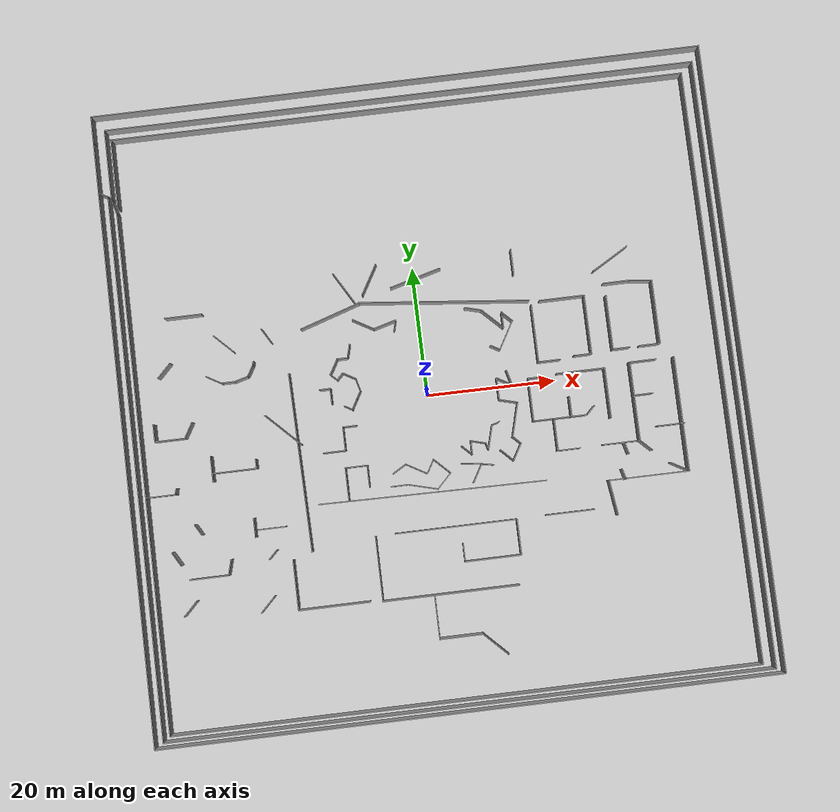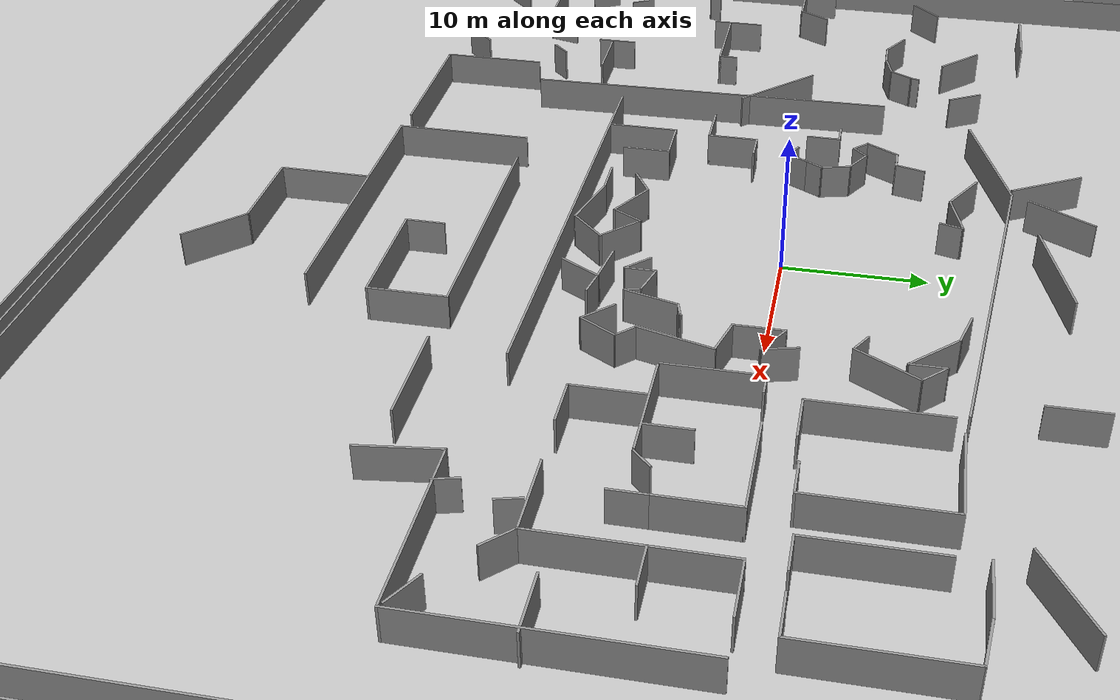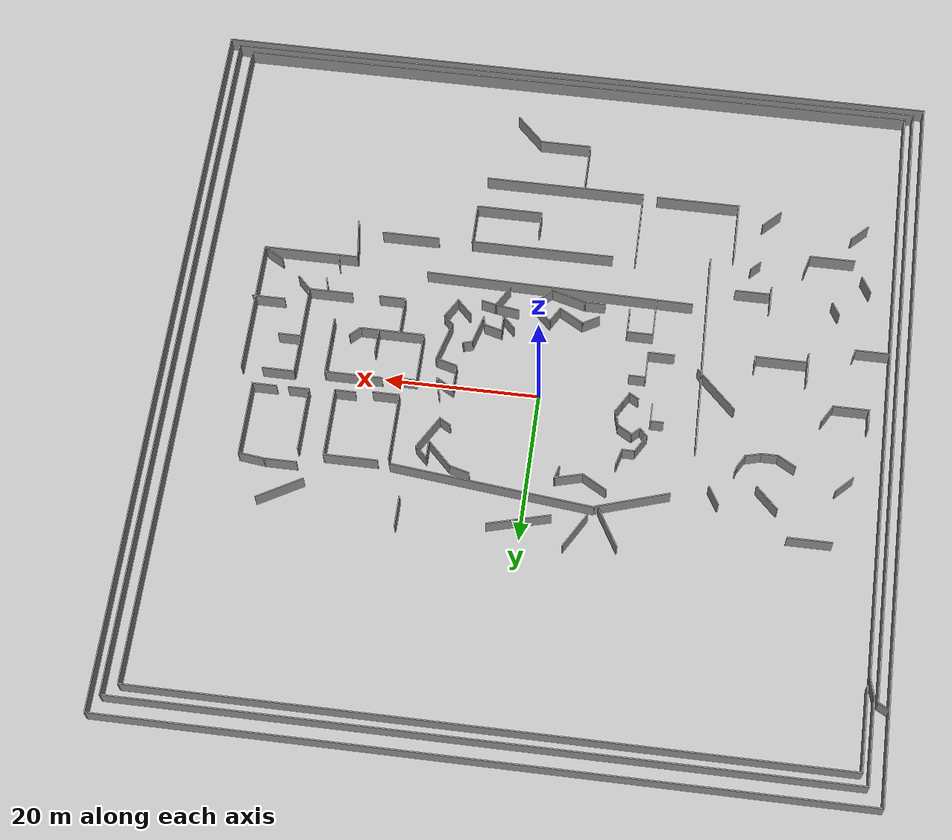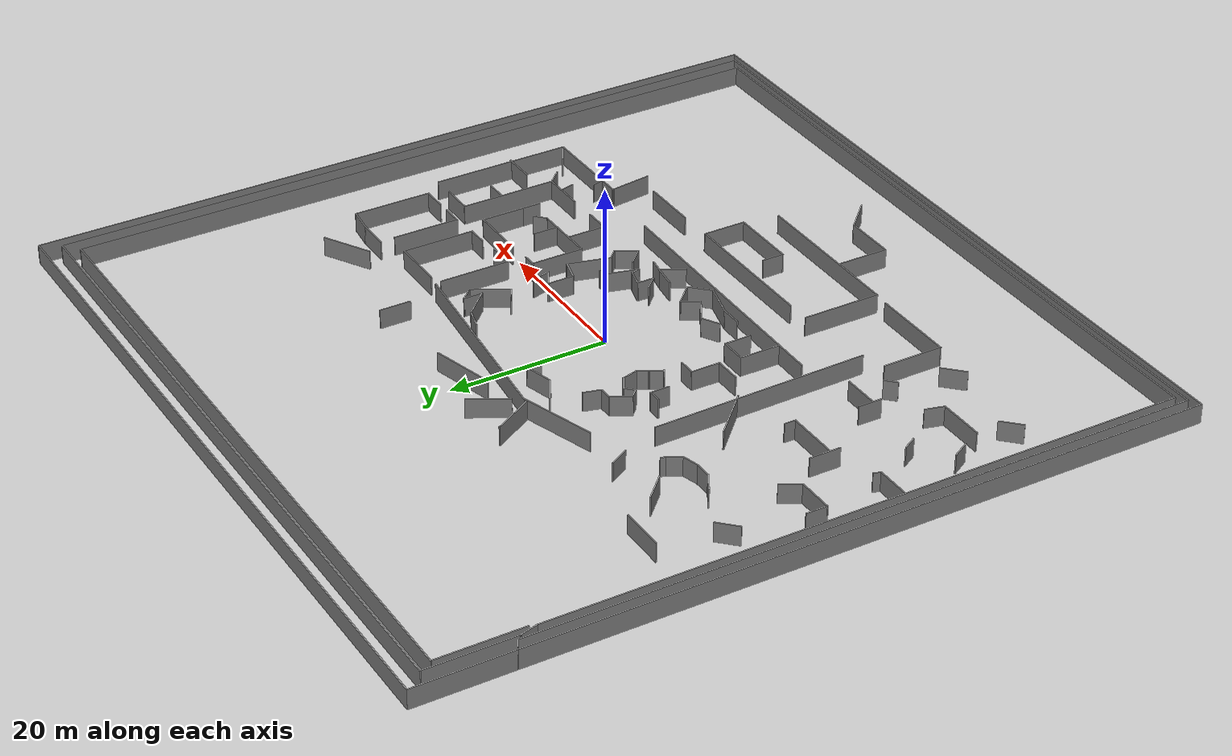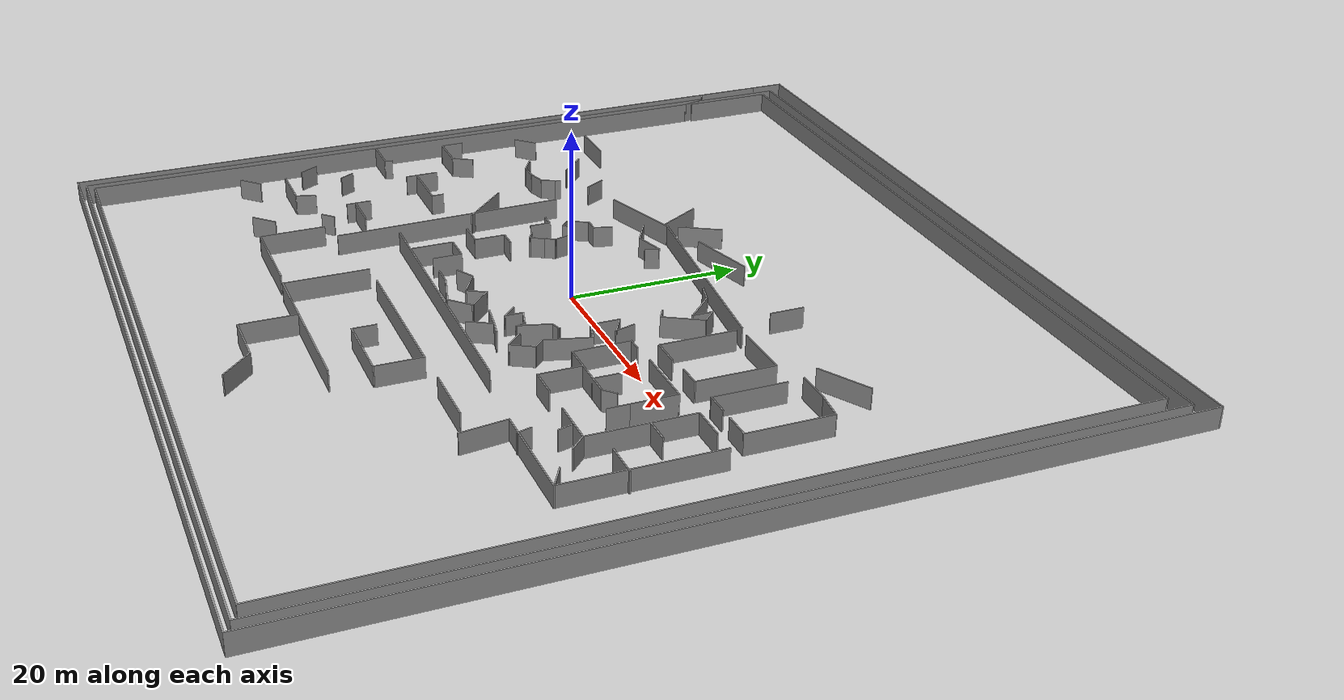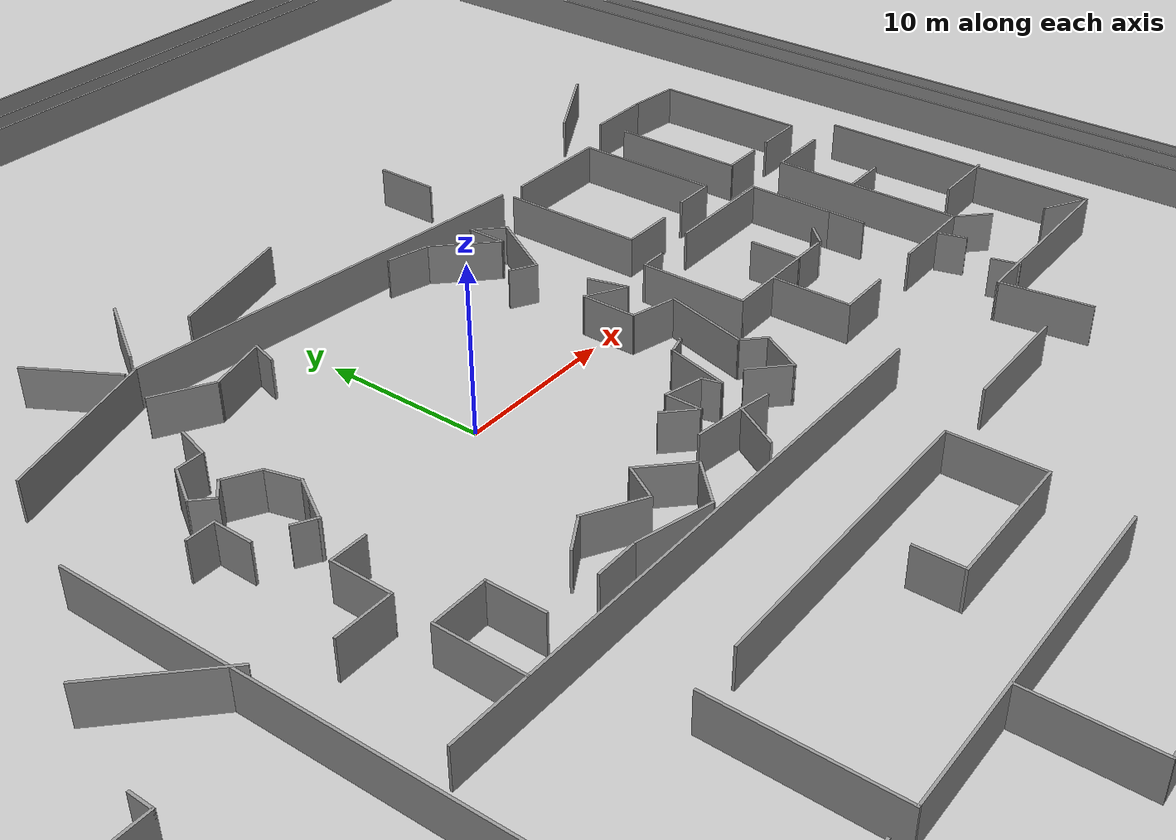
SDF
<?xml version='1.0'?>
<sdf version='1.6'>
  <model name='zee_floor'>
    <pose frame=''>0.886578 0.586712 0 0 -0 0</pose>
    <link name='Wall_0'>
      <collision name='Wall_0_Collision'>
        <geometry>
          <box>
            <size>26.4253 0.15 2.5</size>
          </box>
        </geometry>
        <pose frame=''>0 0 1.25 0 -0 0</pose>
      </collision>
      <visual name='Wall_0_Visual'>
        <pose frame=''>0 0 1.25 0 -0 0</pose>
        <geometry>
          <box>
            <size>26.4253 0.15 2.5</size>
          </box>
        </geometry>
        <material>
          <script>
            <uri>file://media/materials/scripts/gazebo.material</uri>
            <name>Gazebo/Grey</name>
          </script>
          <ambient>1 1 1 1</ambient>
        </material>
        <meta>
          <layer>0</layer>
        </meta>
      </visual>
      <pose frame=''>3.36463 13.4505 0 0 -0 -0.104972</pose>
    </link>
    <link name='Wall_109'>
      <collision name='Wall_109_Collision'>
        <geometry>
          <box>
            <size>2 0.15 2.5</size>
          </box>
        </geometry>
        <pose frame=''>0 0 1.25 0 -0 0</pose>
      </collision>
      <visual name='Wall_109_Visual'>
        <pose frame=''>0 0 1.25 0 -0 0</pose>
        <geometry>
          <box>
            <size>2 0.15 2.5</size>
          </box>
        </geometry>
        <material>
          <script>
            <uri>file://media/materials/scripts/gazebo.material</uri>
            <name>Gazebo/Grey</name>
          </script>
          <ambient>1 1 1 1</ambient>
        </material>
        <meta>
          <layer>0</layer>
        </meta>
      </visual>
      <pose frame=''>-37.8806 -16.8796 0 0 -0 2.0944</pose>
    </link>
    <link name='Wall_11'>
      <collision name='Wall_11_Collision'>
        <geometry>
          <box>
            <size>3.5 0.15 2.5</size>
          </box>
        </geometry>
        <pose frame=''>0 0 1.25 0 -0 0</pose>
      </collision>
      <visual name='Wall_11_Visual'>
        <pose frame=''>0 0 1.25 0 -0 0</pose>
        <geometry>
          <box>
            <size>3.5 0.15 2.5</size>
          </box>
        </geometry>
        <material>
          <script>
            <uri>file://media/materials/scripts/gazebo.material</uri>
            <name>Gazebo/Grey</name>
          </script>
          <ambient>1 1 1 1</ambient>
        </material>
        <meta>
          <layer>0</layer>
        </meta>
      </visual>
      <pose frame=''>-15.9639 -7.56174 0 0 -0 0</pose>
    </link>
    <link name='Wall_112'>
      <collision name='Wall_112_Collision'>
        <geometry>
          <box>
            <size>6.75 0.15 2.5</size>
          </box>
        </geometry>
        <pose frame=''>0 0 1.25 0 -0 0</pose>
      </collision>
      <visual name='Wall_112_Visual'>
        <pose frame=''>0 0 1.25 0 -0 0</pose>
        <geometry>
          <box>
            <size>6.75 0.15 2.5</size>
          </box>
        </geometry>
        <material>
          <script>
            <uri>file://media/materials/scripts/gazebo.material</uri>
            <name>Gazebo/Grey</name>
          </script>
          <ambient>1 1 1 1</ambient>
        </material>
        <meta>
          <layer>0</layer>
        </meta>
      </visual>
      <pose frame=''>-31.3744 -8.64784 0 0 -0 0</pose>
    </link>
    <link name='Wall_113'>
      <collision name='Wall_113_Collision'>
        <geometry>
          <box>
            <size>1.5 0.15 2.5</size>
          </box>
        </geometry>
        <pose frame=''>0 0 1.25 0 -0 0</pose>
      </collision>
      <visual name='Wall_113_Visual'>
        <pose frame=''>0 0 1.25 0 -0 0</pose>
        <geometry>
          <box>
            <size>1.5 0.15 2.5</size>
          </box>
        </geometry>
        <material>
          <script>
            <uri>file://media/materials/scripts/gazebo.material</uri>
            <name>Gazebo/Grey</name>
          </script>
          <ambient>1 1 1 1</ambient>
        </material>
        <meta>
          <layer>0</layer>
        </meta>
      </visual>
      <pose frame=''>-28.0744 -7.97284 0 0 -0 1.5708</pose>
    </link>
    <link name='Wall_12'>
      <collision name='Wall_12_Collision'>
        <geometry>
          <box>
            <size>3.75 0.15 2.5</size>
          </box>
        </geometry>
        <pose frame=''>0 0 1.25 0 -0 0</pose>
      </collision>
      <visual name='Wall_12_Visual'>
        <pose frame=''>0 0 1.25 0 -0 0</pose>
        <geometry>
          <box>
            <size>3.75 0.15 2.5</size>
          </box>
        </geometry>
        <material>
          <script>
            <uri>file://media/materials/scripts/gazebo.material</uri>
            <name>Gazebo/Grey</name>
          </script>
          <ambient>1 1 1 1</ambient>
        </material>
        <meta>
          <layer>0</layer>
        </meta>
      </visual>
      <pose frame=''>-14.2889 -5.76174 0 0 -0 1.5708</pose>
    </link>
    <link name='Wall_127'>
      <collision name='Wall_127_Collision'>
        <geometry>
          <box>
            <size>93.5 0.15 2.5</size>
          </box>
        </geometry>
        <pose frame=''>0 0 1.25 0 -0 0</pose>
      </collision>
      <visual name='Wall_127_Visual'>
        <pose frame=''>0 0 1.25 0 -0 0</pose>
        <geometry>
          <box>
            <size>93.5 0.15 2.5</size>
          </box>
        </geometry>
        <material>
          <script>
            <uri>file://media/materials/scripts/gazebo.material</uri>
            <name>Gazebo/Grey</name>
          </script>
          <ambient>1 1 1 1</ambient>
        </material>
        <meta>
          <layer>0</layer>
        </meta>
      </visual>
      <pose frame=''>-47.7863 -2.125 0 0 -0 -1.5708</pose>
    </link>
    <link name='Wall_128'>
      <collision name='Wall_128_Collision'>
        <geometry>
          <box>
            <size>95.75 0.15 2.5</size>
          </box>
        </geometry>
        <pose frame=''>0 0 1.25 0 -0 0</pose>
      </collision>
      <visual name='Wall_128_Visual'>
        <pose frame=''>0 0 1.25 0 -0 0</pose>
        <geometry>
          <box>
            <size>95.75 0.15 2.5</size>
          </box>
        </geometry>
        <material>
          <script>
            <uri>file://media/materials/scripts/gazebo.material</uri>
            <name>Gazebo/Grey</name>
          </script>
          <ambient>1 1 1 1</ambient>
        </material>
        <meta>
          <layer>0</layer>
        </meta>
      </visual>
      <pose frame=''>0.013723 -48.8 0 0 -0 0</pose>
    </link>
    <link name='Wall_129'>
      <collision name='Wall_129_Collision'>
        <geometry>
          <box>
            <size>97.75 0.15 2.5</size>
          </box>
        </geometry>
        <pose frame=''>0 0 1.25 0 -0 0</pose>
      </collision>
      <visual name='Wall_129_Visual'>
        <pose frame=''>0 0 1.25 0 -0 0</pose>
        <geometry>
          <box>
            <size>97.75 0.15 2.5</size>
          </box>
        </geometry>
        <material>
          <script>
            <uri>file://media/materials/scripts/gazebo.material</uri>
            <name>Gazebo/Grey</name>
          </script>
          <ambient>1 1 1 1</ambient>
        </material>
        <meta>
          <layer>0</layer>
        </meta>
      </visual>
      <pose frame=''>47.8137 -0 0 0 -0 1.5708</pose>
    </link>
    <link name='Wall_13'>
      <collision name='Wall_13_Collision'>
        <geometry>
          <box>
            <size>2.25 0.15 2.5</size>
          </box>
        </geometry>
        <pose frame=''>0 0 1.25 0 -0 0</pose>
      </collision>
      <visual name='Wall_13_Visual'>
        <pose frame=''>0 0 1.25 0 -0 0</pose>
        <geometry>
          <box>
            <size>2.25 0.15 2.5</size>
          </box>
        </geometry>
        <material>
          <script>
            <uri>file://media/materials/scripts/gazebo.material</uri>
            <name>Gazebo/Grey</name>
          </script>
          <ambient>1 1 1 1</ambient>
        </material>
        <meta>
          <layer>0</layer>
        </meta>
      </visual>
      <pose frame=''>-13.2389 -3.96174 0 0 -0 0</pose>
    </link>
    <link name='Wall_130'>
      <collision name='Wall_130_Collision'>
        <geometry>
          <box>
            <size>95.75 0.15 2.5</size>
          </box>
        </geometry>
        <pose frame=''>0 0 1.25 0 -0 0</pose>
      </collision>
      <visual name='Wall_130_Visual'>
        <pose frame=''>0 0 1.25 0 -0 0</pose>
        <geometry>
          <box>
            <size>95.75 0.15 2.5</size>
          </box>
        </geometry>
        <material>
          <script>
            <uri>file://media/materials/scripts/gazebo.material</uri>
            <name>Gazebo/Grey</name>
          </script>
          <ambient>1 1 1 1</ambient>
        </material>
        <meta>
          <layer>0</layer>
        </meta>
      </visual>
      <pose frame=''>0.013723 48.8 0 0 -0 3.14159</pose>
    </link>
    <link name='Wall_131'>
      <collision name='Wall_131_Collision'>
        <geometry>
          <box>
            <size>12.25 0.15 2.5</size>
          </box>
        </geometry>
        <pose frame=''>0 0 1.25 0 -0 0</pose>
      </collision>
      <visual name='Wall_131_Visual'>
        <pose frame=''>0 0 1.25 0 -0 0</pose>
        <geometry>
          <box>
            <size>12.25 0.15 2.5</size>
          </box>
        </geometry>
        <material>
          <script>
            <uri>file://media/materials/scripts/gazebo.material</uri>
            <name>Gazebo/Grey</name>
          </script>
          <ambient>1 1 1 1</ambient>
        </material>
        <meta>
          <layer>0</layer>
        </meta>
      </visual>
      <pose frame=''>-47.7863 42.75 0 0 -0 -1.5708</pose>
    </link>
    <link name='Wall_132'>
      <collision name='Wall_132_Collision'>
        <geometry>
          <box>
            <size>1.75 0.15 2.5</size>
          </box>
        </geometry>
        <pose frame=''>0 0 1.25 0 -0 0</pose>
      </collision>
      <visual name='Wall_132_Visual'>
        <pose frame=''>0 0 1.25 0 -0 0</pose>
        <geometry>
          <box>
            <size>1.75 0.15 2.5</size>
          </box>
        </geometry>
        <material>
          <script>
            <uri>file://media/materials/scripts/gazebo.material</uri>
            <name>Gazebo/Grey</name>
          </script>
          <ambient>1 1 1 1</ambient>
        </material>
        <meta>
          <layer>0</layer>
        </meta>
      </visual>
      <pose frame=''>-47.0935 36.3 0 0 -0 -0.523599</pose>
    </link>
    <link name='Wall_133'>
      <collision name='Wall_133_Collision'>
        <geometry>
          <box>
            <size>84 0.15 2.5</size>
          </box>
        </geometry>
        <pose frame=''>0 0 1.25 0 -0 0</pose>
      </collision>
      <visual name='Wall_133_Visual'>
        <pose frame=''>0 0 1.25 0 -0 0</pose>
        <geometry>
          <box>
            <size>84 0.15 2.5</size>
          </box>
        </geometry>
        <material>
          <script>
            <uri>file://media/materials/scripts/gazebo.material</uri>
            <name>Gazebo/Grey</name>
          </script>
          <ambient>1 1 1 1</ambient>
        </material>
        <meta>
          <layer>0</layer>
        </meta>
      </visual>
      <pose frame=''>-46.4006 -6.025 0 0 -0 -1.5708</pose>
    </link>
    <link name='Wall_134'>
      <collision name='Wall_134_Collision'>
        <geometry>
          <box>
            <size>93 0.15 2.5</size>
          </box>
        </geometry>
        <pose frame=''>0 0 1.25 0 -0 0</pose>
      </collision>
      <visual name='Wall_134_Visual'>
        <pose frame=''>0 0 1.25 0 -0 0</pose>
        <geometry>
          <box>
            <size>93 0.15 2.5</size>
          </box>
        </geometry>
        <material>
          <script>
            <uri>file://media/materials/scripts/gazebo.material</uri>
            <name>Gazebo/Grey</name>
          </script>
          <ambient>1 1 1 1</ambient>
        </material>
        <meta>
          <layer>0</layer>
        </meta>
      </visual>
      <pose frame=''>0.024363 -47.95 0 0 -0 0</pose>
    </link>
    <link name='Wall_135'>
      <collision name='Wall_135_Collision'>
        <geometry>
          <box>
            <size>94.5 0.15 2.5</size>
          </box>
        </geometry>
        <pose frame=''>0 0 1.25 0 -0 0</pose>
      </collision>
      <visual name='Wall_135_Visual'>
        <pose frame=''>0 0 1.25 0 -0 0</pose>
        <geometry>
          <box>
            <size>94.5 0.15 2.5</size>
          </box>
        </geometry>
        <material>
          <script>
            <uri>file://media/materials/scripts/gazebo.material</uri>
            <name>Gazebo/Grey</name>
          </script>
          <ambient>1 1 1 1</ambient>
        </material>
        <meta>
          <layer>0</layer>
        </meta>
      </visual>
      <pose frame=''>46.4494 -0.775 0 0 -0 1.5708</pose>
    </link>
    <link name='Wall_136'>
      <collision name='Wall_136_Collision'>
        <geometry>
          <box>
            <size>92.5 0.15 2.5</size>
          </box>
        </geometry>
        <pose frame=''>0 0 1.25 0 -0 0</pose>
      </collision>
      <visual name='Wall_136_Visual'>
        <pose frame=''>0 0 1.25 0 -0 0</pose>
        <geometry>
          <box>
            <size>92.5 0.15 2.5</size>
          </box>
        </geometry>
        <material>
          <script>
            <uri>file://media/materials/scripts/gazebo.material</uri>
            <name>Gazebo/Grey</name>
          </script>
          <ambient>1 1 1 1</ambient>
        </material>
        <meta>
          <layer>0</layer>
        </meta>
      </visual>
      <pose frame=''>0.274363 46.4 0 0 -0 3.14159</pose>
    </link>
    <link name='Wall_137'>
      <collision name='Wall_137_Collision'>
        <geometry>
          <box>
            <size>11.25 0.15 2.5</size>
          </box>
        </geometry>
        <pose frame=''>0 0 1.25 0 -0 0</pose>
      </collision>
      <visual name='Wall_137_Visual'>
        <pose frame=''>0 0 1.25 0 -0 0</pose>
        <geometry>
          <box>
            <size>11.25 0.15 2.5</size>
          </box>
        </geometry>
        <material>
          <script>
            <uri>file://media/materials/scripts/gazebo.material</uri>
            <name>Gazebo/Grey</name>
          </script>
          <ambient>1 1 1 1</ambient>
        </material>
        <meta>
          <layer>0</layer>
        </meta>
      </visual>
      <pose frame=''>-45.9006 40.85 0 0 -0 -1.5708</pose>
    </link>
    <link name='Wall_138'>
      <collision name='Wall_138_Collision'>
        <geometry>
          <box>
            <size>2.5 0.15 2.5</size>
          </box>
        </geometry>
        <pose frame=''>0 0 1.25 0 -0 0</pose>
      </collision>
      <visual name='Wall_138_Visual'>
        <pose frame=''>0 0 1.25 0 -0 0</pose>
        <geometry>
          <box>
            <size>2.5 0.15 2.5</size>
          </box>
        </geometry>
        <material>
          <script>
            <uri>file://media/materials/scripts/gazebo.material</uri>
            <name>Gazebo/Grey</name>
          </script>
          <ambient>1 1 1 1</ambient>
        </material>
        <meta>
          <layer>0</layer>
        </meta>
      </visual>
      <pose frame=''>-45.5965 34.165 0 0 -0 -1.309</pose>
    </link>
    <link name='Wall_139'>
      <collision name='Wall_139_Collision'>
        <geometry>
          <box>
            <size>80.25 0.15 2.5</size>
          </box>
        </geometry>
        <pose frame=''>0 0 1.25 0 -0 0</pose>
      </collision>
      <visual name='Wall_139_Visual'>
        <pose frame=''>0 0 1.25 0 -0 0</pose>
        <geometry>
          <box>
            <size>80.25 0.15 2.5</size>
          </box>
        </geometry>
        <material>
          <script>
            <uri>file://media/materials/scripts/gazebo.material</uri>
            <name>Gazebo/Grey</name>
          </script>
          <ambient>1 1 1 1</ambient>
        </material>
        <meta>
          <layer>0</layer>
        </meta>
      </visual>
      <pose frame=''>-45.2924 -7.01993 0 0 -0 -1.5708</pose>
    </link>
    <link name='Wall_140'>
      <collision name='Wall_140_Collision'>
        <geometry>
          <box>
            <size>90 0.15 2.5</size>
          </box>
        </geometry>
        <pose frame=''>0 0 1.25 0 -0 0</pose>
      </collision>
      <visual name='Wall_140_Visual'>
        <pose frame=''>0 0 1.25 0 -0 0</pose>
        <geometry>
          <box>
            <size>90 0.15 2.5</size>
          </box>
        </geometry>
        <material>
          <script>
            <uri>file://media/materials/scripts/gazebo.material</uri>
            <name>Gazebo/Grey</name>
          </script>
          <ambient>1 1 1 1</ambient>
        </material>
        <meta>
          <layer>0</layer>
        </meta>
      </visual>
      <pose frame=''>-0.367412 -47.0699 0 0 -0 0</pose>
    </link>
    <link name='Wall_141'>
      <collision name='Wall_141_Collision'>
        <geometry>
          <box>
            <size>92 0.15 2.5</size>
          </box>
        </geometry>
        <pose frame=''>0 0 1.25 0 -0 0</pose>
      </collision>
      <visual name='Wall_141_Visual'>
        <pose frame=''>0 0 1.25 0 -0 0</pose>
        <geometry>
          <box>
            <size>92 0.15 2.5</size>
          </box>
        </geometry>
        <material>
          <script>
            <uri>file://media/materials/scripts/gazebo.material</uri>
            <name>Gazebo/Grey</name>
          </script>
          <ambient>1 1 1 1</ambient>
        </material>
        <meta>
          <layer>0</layer>
        </meta>
      </visual>
      <pose frame=''>44.5576 -1.14493 0 0 -0 1.5708</pose>
    </link>
    <link name='Wall_142'>
      <collision name='Wall_142_Collision'>
        <geometry>
          <box>
            <size>89.75 0.15 2.5</size>
          </box>
        </geometry>
        <pose frame=''>0 0 1.25 0 -0 0</pose>
      </collision>
      <visual name='Wall_142_Visual'>
        <pose frame=''>0 0 1.25 0 -0 0</pose>
        <geometry>
          <box>
            <size>89.75 0.15 2.5</size>
          </box>
        </geometry>
        <material>
          <script>
            <uri>file://media/materials/scripts/gazebo.material</uri>
            <name>Gazebo/Grey</name>
          </script>
          <ambient>1 1 1 1</ambient>
        </material>
        <meta>
          <layer>0</layer>
        </meta>
      </visual>
      <pose frame=''>-0.242412 44.7801 0 0 -0 3.14159</pose>
    </link>
    <link name='Wall_143'>
      <collision name='Wall_143_Collision'>
        <geometry>
          <box>
            <size>11 0.15 2.5</size>
          </box>
        </geometry>
        <pose frame=''>0 0 1.25 0 -0 0</pose>
      </collision>
      <visual name='Wall_143_Visual'>
        <pose frame=''>0 0 1.25 0 -0 0</pose>
        <geometry>
          <box>
            <size>11 0.15 2.5</size>
          </box>
        </geometry>
        <material>
          <script>
            <uri>file://media/materials/scripts/gazebo.material</uri>
            <name>Gazebo/Grey</name>
          </script>
          <ambient>1 1 1 1</ambient>
        </material>
        <meta>
          <layer>0</layer>
        </meta>
      </visual>
      <pose frame=''>-45.0424 39.3551 0 0 -0 -1.5708</pose>
    </link>
    <link name='Wall_145'>
      <collision name='Wall_145_Collision'>
        <geometry>
          <box>
            <size>18.75 0.15 2.5</size>
          </box>
        </geometry>
        <pose frame=''>0 0 1.25 0 -0 0</pose>
      </collision>
      <visual name='Wall_145_Visual'>
        <pose frame=''>0 0 1.25 0 -0 0</pose>
        <geometry>
          <box>
            <size>18.75 0.15 2.5</size>
          </box>
        </geometry>
        <material>
          <script>
            <uri>file://media/materials/scripts/gazebo.material</uri>
            <name>Gazebo/Grey</name>
          </script>
          <ambient>1 1 1 1</ambient>
        </material>
        <meta>
          <layer>0</layer>
        </meta>
      </visual>
      <pose frame=''>1.13676 -21.0403 0 0 -0 0</pose>
    </link>
    <link name='Wall_146'>
      <collision name='Wall_146_Collision'>
        <geometry>
          <box>
            <size>5.45275 0.15 2.5</size>
          </box>
        </geometry>
        <pose frame=''>0 0 1.25 0 -0 0</pose>
      </collision>
      <visual name='Wall_146_Visual'>
        <pose frame=''>0 0 1.25 0 -0 0</pose>
        <geometry>
          <box>
            <size>5.45275 0.15 2.5</size>
          </box>
        </geometry>
        <material>
          <script>
            <uri>file://media/materials/scripts/gazebo.material</uri>
            <name>Gazebo/Grey</name>
          </script>
          <ambient>1 1 1 1</ambient>
        </material>
        <meta>
          <layer>0</layer>
        </meta>
      </visual>
      <pose frame=''>10.4368 -23.6916 0 0 -0 -1.5708</pose>
    </link>
    <link name='Wall_147'>
      <collision name='Wall_147_Collision'>
        <geometry>
          <box>
            <size>8.75 0.15 2.5</size>
          </box>
        </geometry>
        <pose frame=''>0 0 1.25 0 -0 0</pose>
      </collision>
      <visual name='Wall_147_Visual'>
        <pose frame=''>0 0 1.25 0 -0 0</pose>
        <geometry>
          <box>
            <size>8.75 0.15 2.5</size>
          </box>
        </geometry>
        <material>
          <script>
            <uri>file://media/materials/scripts/gazebo.material</uri>
            <name>Gazebo/Grey</name>
          </script>
          <ambient>1 1 1 1</ambient>
        </material>
        <meta>
          <layer>0</layer>
        </meta>
      </visual>
      <pose frame=''>6.13676 -26.4845 0 0 -0 3.14159</pose>
    </link>
    <link name='Wall_148'>
      <collision name='Wall_148_Collision'>
        <geometry>
          <box>
            <size>2.70275 0.15 2.5</size>
          </box>
        </geometry>
        <pose frame=''>0 0 1.25 0 -0 0</pose>
      </collision>
      <visual name='Wall_148_Visual'>
        <pose frame=''>0 0 1.25 0 -0 0</pose>
        <geometry>
          <box>
            <size>2.70275 0.15 2.5</size>
          </box>
        </geometry>
        <material>
          <script>
            <uri>file://media/materials/scripts/gazebo.material</uri>
            <name>Gazebo/Grey</name>
          </script>
          <ambient>1 1 1 1</ambient>
        </material>
        <meta>
          <layer>0</layer>
        </meta>
      </visual>
      <pose frame=''>1.83676 -25.0666 0 0 -0 1.5708</pose>
    </link>
    <link name='Wall_15'>
      <collision name='Wall_15_Collision'>
        <geometry>
          <box>
            <size>1.75 0.15 2.5</size>
          </box>
        </geometry>
        <pose frame=''>0 0 1.25 0 -0 0</pose>
      </collision>
      <visual name='Wall_15_Visual'>
        <pose frame=''>0 0 1.25 0 -0 0</pose>
        <geometry>
          <box>
            <size>1.75 0.15 2.5</size>
          </box>
        </geometry>
        <material>
          <script>
            <uri>file://media/materials/scripts/gazebo.material</uri>
            <name>Gazebo/Grey</name>
          </script>
          <ambient>1 1 1 1</ambient>
        </material>
        <meta>
          <layer>0</layer>
        </meta>
      </visual>
      <pose frame=''>-16.3464 2.1476 0 0 -0 0</pose>
    </link>
    <link name='Wall_151'>
      <collision name='Wall_151_Collision'>
        <geometry>
          <box>
            <size>21 0.15 2.5</size>
          </box>
        </geometry>
        <pose frame=''>0 0 1.25 0 -0 0</pose>
      </collision>
      <visual name='Wall_151_Visual'>
        <pose frame=''>0 0 1.25 0 -0 0</pose>
        <geometry>
          <box>
            <size>21 0.15 2.5</size>
          </box>
        </geometry>
        <material>
          <script>
            <uri>file://media/materials/scripts/gazebo.material</uri>
            <name>Gazebo/Grey</name>
          </script>
          <ambient>1 1 1 1</ambient>
        </material>
        <meta>
          <layer>0</layer>
        </meta>
      </visual>
      <pose frame=''>-0.808756 -30.9593 0 0 -0 3.14159</pose>
    </link>
    <link name='Wall_152'>
      <collision name='Wall_152_Collision'>
        <geometry>
          <box>
            <size>10 0.15 2.5</size>
          </box>
        </geometry>
        <pose frame=''>0 0 1.25 0 -0 0</pose>
      </collision>
      <visual name='Wall_152_Visual'>
        <pose frame=''>0 0 1.25 0 -0 0</pose>
        <geometry>
          <box>
            <size>10 0.15 2.5</size>
          </box>
        </geometry>
        <material>
          <script>
            <uri>file://media/materials/scripts/gazebo.material</uri>
            <name>Gazebo/Grey</name>
          </script>
          <ambient>1 1 1 1</ambient>
        </material>
        <meta>
          <layer>0</layer>
        </meta>
      </visual>
      <pose frame=''>-11.2338 -26.0343 0 0 -0 1.5708</pose>
    </link>
    <link name='Wall_154'>
      <collision name='Wall_154_Collision'>
        <geometry>
          <box>
            <size>11 0.15 2.5</size>
          </box>
        </geometry>
        <pose frame=''>0 0 1.25 0 -0 0</pose>
      </collision>
      <visual name='Wall_154_Visual'>
        <pose frame=''>0 0 1.25 0 -0 0</pose>
        <geometry>
          <box>
            <size>11 0.15 2.5</size>
          </box>
        </geometry>
        <material>
          <script>
            <uri>file://media/materials/scripts/gazebo.material</uri>
            <name>Gazebo/Grey</name>
          </script>
          <ambient>1 1 1 1</ambient>
        </material>
        <meta>
          <layer>0</layer>
        </meta>
      </visual>
      <pose frame=''>-18.6414 -30.7722 0 0 -0 3.14159</pose>
    </link>
    <link name='Wall_155'>
      <collision name='Wall_155_Collision'>
        <geometry>
          <box>
            <size>7.75 0.15 2.5</size>
          </box>
        </geometry>
        <pose frame=''>0 0 1.25 0 -0 0</pose>
      </collision>
      <visual name='Wall_155_Visual'>
        <pose frame=''>0 0 1.25 0 -0 0</pose>
        <geometry>
          <box>
            <size>7.75 0.15 2.5</size>
          </box>
        </geometry>
        <material>
          <script>
            <uri>file://media/materials/scripts/gazebo.material</uri>
            <name>Gazebo/Grey</name>
          </script>
          <ambient>1 1 1 1</ambient>
        </material>
        <meta>
          <layer>0</layer>
        </meta>
      </visual>
      <pose frame=''>-24.0664 -26.9722 0 0 -0 1.5708</pose>
    </link>
    <link name='Wall_157'>
      <collision name='Wall_157_Collision'>
        <geometry>
          <box>
            <size>6.75 0.15 2.5</size>
          </box>
        </geometry>
        <pose frame=''>0 0 1.25 0 -0 0</pose>
      </collision>
      <visual name='Wall_157_Visual'>
        <pose frame=''>0 0 1.25 0 -0 0</pose>
        <geometry>
          <box>
            <size>6.75 0.15 2.5</size>
          </box>
        </geometry>
        <material>
          <script>
            <uri>file://media/materials/scripts/gazebo.material</uri>
            <name>Gazebo/Grey</name>
          </script>
          <ambient>1 1 1 1</ambient>
        </material>
        <meta>
          <layer>0</layer>
        </meta>
      </visual>
      <pose frame=''>-3.36909 -34.2723 0 0 -0 -1.5708</pose>
    </link>
    <link name='Wall_158'>
      <collision name='Wall_158_Collision'>
        <geometry>
          <box>
            <size>6.75 0.15 2.5</size>
          </box>
        </geometry>
        <pose frame=''>0 0 1.25 0 -0 0</pose>
      </collision>
      <visual name='Wall_158_Visual'>
        <pose frame=''>0 0 1.25 0 -0 0</pose>
        <geometry>
          <box>
            <size>6.75 0.15 2.5</size>
          </box>
        </geometry>
        <material>
          <script>
            <uri>file://media/materials/scripts/gazebo.material</uri>
            <name>Gazebo/Grey</name>
          </script>
          <ambient>1 1 1 1</ambient>
        </material>
        <meta>
          <layer>0</layer>
        </meta>
      </visual>
      <pose frame=''>-0.069089 -37.5723 0 0 -0 0</pose>
    </link>
    <link name='Wall_159'>
      <collision name='Wall_159_Collision'>
        <geometry>
          <box>
            <size>5 0.15 2.5</size>
          </box>
        </geometry>
        <pose frame=''>0 0 1.25 0 -0 0</pose>
      </collision>
      <visual name='Wall_159_Visual'>
        <pose frame=''>0 0 1.25 0 -0 0</pose>
        <geometry>
          <box>
            <size>5 0.15 2.5</size>
          </box>
        </geometry>
        <material>
          <script>
            <uri>file://media/materials/scripts/gazebo.material</uri>
            <name>Gazebo/Grey</name>
          </script>
          <ambient>1 1 1 1</ambient>
        </material>
        <meta>
          <layer>0</layer>
        </meta>
      </visual>
      <pose frame=''>4.94564 -39.287 0 0 -0 -0.785398</pose>
    </link>
    <link name='Wall_16'>
      <collision name='Wall_16_Collision'>
        <geometry>
          <box>
            <size>2.5 0.15 2.5</size>
          </box>
        </geometry>
        <pose frame=''>0 0 1.25 0 -0 0</pose>
      </collision>
      <visual name='Wall_16_Visual'>
        <pose frame=''>0 0 1.25 0 -0 0</pose>
        <geometry>
          <box>
            <size>2.5 0.15 2.5</size>
          </box>
        </geometry>
        <material>
          <script>
            <uri>file://media/materials/scripts/gazebo.material</uri>
            <name>Gazebo/Grey</name>
          </script>
          <ambient>1 1 1 1</ambient>
        </material>
        <meta>
          <layer>0</layer>
        </meta>
      </visual>
      <pose frame=''>-15.5464 0.972602 0 0 -0 -1.5708</pose>
    </link>
    <link name='Wall_163'>
      <collision name='Wall_163_Collision'>
        <geometry>
          <box>
            <size>5.75 0.15 2.5</size>
          </box>
        </geometry>
        <pose frame=''>0 0 1.25 0 -0 0</pose>
      </collision>
      <visual name='Wall_163_Visual'>
        <pose frame=''>0 0 1.25 0 -0 0</pose>
        <geometry>
          <box>
            <size>5.75 0.15 2.5</size>
          </box>
        </geometry>
        <material>
          <script>
            <uri>file://media/materials/scripts/gazebo.material</uri>
            <name>Gazebo/Grey</name>
          </script>
          <ambient>1 1 1 1</ambient>
        </material>
        <meta>
          <layer>0</layer>
        </meta>
      </visual>
      <pose frame=''>-11.6937 17.3049 0 0 -0 2.0944</pose>
    </link>
    <link name='Wall_165'>
      <collision name='Wall_165_Collision'>
        <geometry>
          <box>
            <size>5.25 0.15 2.5</size>
          </box>
        </geometry>
        <pose frame=''>0 0 1.25 0 -0 0</pose>
      </collision>
      <visual name='Wall_165_Visual'>
        <pose frame=''>0 0 1.25 0 -0 0</pose>
        <geometry>
          <box>
            <size>5.25 0.15 2.5</size>
          </box>
        </geometry>
        <material>
          <script>
            <uri>file://media/materials/scripts/gazebo.material</uri>
            <name>Gazebo/Grey</name>
          </script>
          <ambient>1 1 1 1</ambient>
        </material>
        <meta>
          <layer>0</layer>
        </meta>
      </visual>
      <pose frame=''>-7.70866 18.2113 0 0 -0 1.0472</pose>
    </link>
    <link name='Wall_167'>
      <collision name='Wall_167_Collision'>
        <geometry>
          <box>
            <size>8.25 0.15 2.5</size>
          </box>
        </geometry>
        <pose frame=''>0 0 1.25 0 -0 0</pose>
      </collision>
      <visual name='Wall_167_Visual'>
        <pose frame=''>0 0 1.25 0 -0 0</pose>
        <geometry>
          <box>
            <size>8.25 0.15 2.5</size>
          </box>
        </geometry>
        <material>
          <script>
            <uri>file://media/materials/scripts/gazebo.material</uri>
            <name>Gazebo/Grey</name>
          </script>
          <ambient>1 1 1 1</ambient>
        </material>
        <meta>
          <layer>0</layer>
        </meta>
      </visual>
      <pose frame=''>-0.580004 17.6126 0 0 -0 0.261799</pose>
    </link>
    <link name='Wall_169'>
      <collision name='Wall_169_Collision'>
        <geometry>
          <box>
            <size>4 0.15 2.5</size>
          </box>
        </geometry>
        <pose frame=''>0 0 1.25 0 -0 0</pose>
      </collision>
      <visual name='Wall_169_Visual'>
        <pose frame=''>0 0 1.25 0 -0 0</pose>
        <geometry>
          <box>
            <size>4 0.15 2.5</size>
          </box>
        </geometry>
        <material>
          <script>
            <uri>file://media/materials/scripts/gazebo.material</uri>
            <name>Gazebo/Grey</name>
          </script>
          <ambient>1 1 1 1</ambient>
        </material>
        <meta>
          <layer>0</layer>
        </meta>
      </visual>
      <pose frame=''>14.5975 18.3023 0 0 -0 1.5708</pose>
    </link>
    <link name='Wall_171'>
      <collision name='Wall_171_Collision'>
        <geometry>
          <box>
            <size>6.5 0.15 2.5</size>
          </box>
        </geometry>
        <pose frame=''>0 0 1.25 0 -0 0</pose>
      </collision>
      <visual name='Wall_171_Visual'>
        <pose frame=''>0 0 1.25 0 -0 0</pose>
        <geometry>
          <box>
            <size>6.5 0.15 2.5</size>
          </box>
        </geometry>
        <material>
          <script>
            <uri>file://media/materials/scripts/gazebo.material</uri>
            <name>Gazebo/Grey</name>
          </script>
          <ambient>1 1 1 1</ambient>
        </material>
        <meta>
          <layer>0</layer>
        </meta>
      </visual>
      <pose frame=''>29.6992 17.029 0 0 -0 0.523599</pose>
    </link>
    <link name='Wall_173'>
      <collision name='Wall_173_Collision'>
        <geometry>
          <box>
            <size>4.5 0.15 2.5</size>
          </box>
        </geometry>
        <pose frame=''>0 0 1.25 0 -0 0</pose>
      </collision>
      <visual name='Wall_173_Visual'>
        <pose frame=''>0 0 1.25 0 -0 0</pose>
        <geometry>
          <box>
            <size>4.5 0.15 2.5</size>
          </box>
        </geometry>
        <material>
          <script>
            <uri>file://media/materials/scripts/gazebo.material</uri>
            <name>Gazebo/Grey</name>
          </script>
          <ambient>1 1 1 1</ambient>
        </material>
        <meta>
          <layer>0</layer>
        </meta>
      </visual>
      <pose frame=''>-26.9007 -17.9776 0 0 -0 0</pose>
    </link>
    <link name='Wall_177'>
      <collision name='Wall_177_Collision'>
        <geometry>
          <box>
            <size>3 0.15 2.5</size>
          </box>
        </geometry>
        <pose frame=''>0 0 1.25 0 -0 0</pose>
      </collision>
      <visual name='Wall_177_Visual'>
        <pose frame=''>0 0 1.25 0 -0 0</pose>
        <geometry>
          <box>
            <size>3 0.15 2.5</size>
          </box>
        </geometry>
        <material>
          <script>
            <uri>file://media/materials/scripts/gazebo.material</uri>
            <name>Gazebo/Grey</name>
          </script>
          <ambient>1 1 1 1</ambient>
        </material>
        <meta>
          <layer>0</layer>
        </meta>
      </visual>
      <pose frame=''>-29.3444 -17.5874 0 0 -0 1.5708</pose>
    </link>
    <link name='Wall_179'>
      <collision name='Wall_179_Collision'>
        <geometry>
          <box>
            <size>6 0.15 2.5</size>
          </box>
        </geometry>
        <pose frame=''>0 0 1.25 0 -0 0</pose>
      </collision>
      <visual name='Wall_179_Visual'>
        <pose frame=''>0 0 1.25 0 -0 0</pose>
        <geometry>
          <box>
            <size>6 0.15 2.5</size>
          </box>
        </geometry>
        <material>
          <script>
            <uri>file://media/materials/scripts/gazebo.material</uri>
            <name>Gazebo/Grey</name>
          </script>
          <ambient>1 1 1 1</ambient>
        </material>
        <meta>
          <layer>0</layer>
        </meta>
      </visual>
      <pose frame=''>-36.9503 -24.2752 0 0 -0 0</pose>
    </link>
    <link name='Wall_18'>
      <collision name='Wall_18_Collision'>
        <geometry>
          <box>
            <size>1.5 0.15 2.5</size>
          </box>
        </geometry>
        <pose frame=''>0 0 1.25 0 -0 0</pose>
      </collision>
      <visual name='Wall_18_Visual'>
        <pose frame=''>0 0 1.25 0 -0 0</pose>
        <geometry>
          <box>
            <size>1.5 0.15 2.5</size>
          </box>
        </geometry>
        <material>
          <script>
            <uri>file://media/materials/scripts/gazebo.material</uri>
            <name>Gazebo/Grey</name>
          </script>
          <ambient>1 1 1 1</ambient>
        </material>
        <meta>
          <layer>0</layer>
        </meta>
      </visual>
      <pose frame=''>-13.0774 -1.1172 0 0 -0 -0.523599</pose>
    </link>
    <link name='Wall_180'>
      <collision name='Wall_180_Collision'>
        <geometry>
          <box>
            <size>2.5 0.15 2.5</size>
          </box>
        </geometry>
        <pose frame=''>0 0 1.25 0 -0 0</pose>
      </collision>
      <visual name='Wall_180_Visual'>
        <pose frame=''>0 0 1.25 0 -0 0</pose>
        <geometry>
          <box>
            <size>2.5 0.15 2.5</size>
          </box>
        </geometry>
        <material>
          <script>
            <uri>file://media/materials/scripts/gazebo.material</uri>
            <name>Gazebo/Grey</name>
          </script>
          <ambient>1 1 1 1</ambient>
        </material>
        <meta>
          <layer>0</layer>
        </meta>
      </visual>
      <pose frame=''>-33.7211 -23.1403 0 0 -0 1.309</pose>
    </link>
    <link name='Wall_182'>
      <collision name='Wall_182_Collision'>
        <geometry>
          <box>
            <size>2.5 0.15 2.5</size>
          </box>
        </geometry>
        <pose frame=''>0 0 1.25 0 -0 0</pose>
      </collision>
      <visual name='Wall_182_Visual'>
        <pose frame=''>0 0 1.25 0 -0 0</pose>
        <geometry>
          <box>
            <size>2.5 0.15 2.5</size>
          </box>
        </geometry>
        <material>
          <script>
            <uri>file://media/materials/scripts/gazebo.material</uri>
            <name>Gazebo/Grey</name>
          </script>
          <ambient>1 1 1 1</ambient>
        </material>
        <meta>
          <layer>0</layer>
        </meta>
      </visual>
      <pose frame=''>-41.6131 -20.9089 0 0 -0 2.0944</pose>
    </link>
    <link name='Wall_185'>
      <collision name='Wall_185_Collision'>
        <geometry>
          <box>
            <size>4 0.15 2.5</size>
          </box>
        </geometry>
        <pose frame=''>0 0 1.25 0 -0 0</pose>
      </collision>
      <visual name='Wall_185_Visual'>
        <pose frame=''>0 0 1.25 0 -0 0</pose>
        <geometry>
          <box>
            <size>4 0.15 2.5</size>
          </box>
        </geometry>
        <material>
          <script>
            <uri>file://media/materials/scripts/gazebo.material</uri>
            <name>Gazebo/Grey</name>
          </script>
          <ambient>1 1 1 1</ambient>
        </material>
        <meta>
          <layer>0</layer>
        </meta>
      </visual>
      <pose frame=''>-34.8589 -7.97311 0 0 -0 1.5708</pose>
    </link>
    <link name='Wall_187'>
      <collision name='Wall_187_Collision'>
        <geometry>
          <box>
            <size>2.75 0.15 2.5</size>
          </box>
        </geometry>
        <pose frame=''>0 0 1.25 0 -0 0</pose>
      </collision>
      <visual name='Wall_187_Visual'>
        <pose frame=''>0 0 1.25 0 -0 0</pose>
        <geometry>
          <box>
            <size>2.75 0.15 2.5</size>
          </box>
        </geometry>
        <material>
          <script>
            <uri>file://media/materials/scripts/gazebo.material</uri>
            <name>Gazebo/Grey</name>
          </script>
          <ambient>1 1 1 1</ambient>
        </material>
        <meta>
          <layer>0</layer>
        </meta>
      </visual>
      <pose frame=''>-43.0551 -1.49284 0 0 -0 -1.5708</pose>
    </link>
    <link name='Wall_188'>
      <collision name='Wall_188_Collision'>
        <geometry>
          <box>
            <size>4.75 0.15 2.5</size>
          </box>
        </geometry>
        <pose frame=''>0 0 1.25 0 -0 0</pose>
      </collision>
      <visual name='Wall_188_Visual'>
        <pose frame=''>0 0 1.25 0 -0 0</pose>
        <geometry>
          <box>
            <size>4.75 0.15 2.5</size>
          </box>
        </geometry>
        <material>
          <script>
            <uri>file://media/materials/scripts/gazebo.material</uri>
            <name>Gazebo/Grey</name>
          </script>
          <ambient>1 1 1 1</ambient>
        </material>
        <meta>
          <layer>0</layer>
        </meta>
      </visual>
      <pose frame=''>-40.7551 -2.79284 0 0 -0 0</pose>
    </link>
    <link name='Wall_189'>
      <collision name='Wall_189_Collision'>
        <geometry>
          <box>
            <size>2.75 0.15 2.5</size>
          </box>
        </geometry>
        <pose frame=''>0 0 1.25 0 -0 0</pose>
      </collision>
      <visual name='Wall_189_Visual'>
        <pose frame=''>0 0 1.25 0 -0 0</pose>
        <geometry>
          <box>
            <size>2.75 0.15 2.5</size>
          </box>
        </geometry>
        <material>
          <script>
            <uri>file://media/materials/scripts/gazebo.material</uri>
            <name>Gazebo/Grey</name>
          </script>
          <ambient>1 1 1 1</ambient>
        </material>
        <meta>
          <layer>0</layer>
        </meta>
      </visual>
      <pose frame=''>-37.8051 -1.667 0 0 -0 1.0472</pose>
    </link>
    <link name='Wall_19'>
      <collision name='Wall_19_Collision'>
        <geometry>
          <box>
            <size>1.88298 0.15 2.5</size>
          </box>
        </geometry>
        <pose frame=''>0 0 1.25 0 -0 0</pose>
      </collision>
      <visual name='Wall_19_Visual'>
        <pose frame=''>0 0 1.25 0 -0 0</pose>
        <geometry>
          <box>
            <size>1.88298 0.15 2.5</size>
          </box>
        </geometry>
        <material>
          <script>
            <uri>file://media/materials/scripts/gazebo.material</uri>
            <name>Gazebo/Grey</name>
          </script>
          <ambient>1 1 1 1</ambient>
        </material>
        <meta>
          <layer>0</layer>
        </meta>
      </visual>
      <pose frame=''>-12.1071 -0.703548 0 0 -0 1.04892</pose>
    </link>
    <link name='Wall_191'>
      <collision name='Wall_191_Collision'>
        <geometry>
          <box>
            <size>4.5 0.15 2.5</size>
          </box>
        </geometry>
        <pose frame=''>0 0 1.25 0 -0 0</pose>
      </collision>
      <visual name='Wall_191_Visual'>
        <pose frame=''>0 0 1.25 0 -0 0</pose>
        <geometry>
          <box>
            <size>4.5 0.15 2.5</size>
          </box>
        </geometry>
        <material>
          <script>
            <uri>file://media/materials/scripts/gazebo.material</uri>
            <name>Gazebo/Grey</name>
          </script>
          <ambient>1 1 1 1</ambient>
        </material>
        <meta>
          <layer>0</layer>
        </meta>
      </visual>
      <pose frame=''>-42.9721 -11.1448 0 0 -0 0</pose>
    </link>
    <link name='Wall_192'>
      <collision name='Wall_192_Collision'>
        <geometry>
          <box>
            <size>1 0.15 2.5</size>
          </box>
        </geometry>
        <pose frame=''>0 0 1.25 0 -0 0</pose>
      </collision>
      <visual name='Wall_192_Visual'>
        <pose frame=''>0 0 1.25 0 -0 0</pose>
        <geometry>
          <box>
            <size>1 0.15 2.5</size>
          </box>
        </geometry>
        <material>
          <script>
            <uri>file://media/materials/scripts/gazebo.material</uri>
            <name>Gazebo/Grey</name>
          </script>
          <ambient>1 1 1 1</ambient>
        </material>
        <meta>
          <layer>0</layer>
        </meta>
      </visual>
      <pose frame=''>-40.6871 -10.7343 0 0 -0 1.309</pose>
    </link>
    <link name='Wall_194'>
      <collision name='Wall_194_Collision'>
        <geometry>
          <box>
            <size>2.75 0.15 2.5</size>
          </box>
        </geometry>
        <pose frame=''>0 0 1.25 0 -0 0</pose>
      </collision>
      <visual name='Wall_194_Visual'>
        <pose frame=''>0 0 1.25 0 -0 0</pose>
        <geometry>
          <box>
            <size>2.75 0.15 2.5</size>
          </box>
        </geometry>
        <material>
          <script>
            <uri>file://media/materials/scripts/gazebo.material</uri>
            <name>Gazebo/Grey</name>
          </script>
          <ambient>1 1 1 1</ambient>
        </material>
        <meta>
          <layer>0</layer>
        </meta>
      </visual>
      <pose frame=''>-33.1476 5.60743 0 0 -0 -0.523599</pose>
    </link>
    <link name='Wall_195'>
      <collision name='Wall_195_Collision'>
        <geometry>
          <box>
            <size>2.25 0.15 2.5</size>
          </box>
        </geometry>
        <pose frame=''>0 0 1.25 0 -0 0</pose>
      </collision>
      <visual name='Wall_195_Visual'>
        <pose frame=''>0 0 1.25 0 -0 0</pose>
        <geometry>
          <box>
            <size>2.25 0.15 2.5</size>
          </box>
        </geometry>
        <material>
          <script>
            <uri>file://media/materials/scripts/gazebo.material</uri>
            <name>Gazebo/Grey</name>
          </script>
          <ambient>1 1 1 1</ambient>
        </material>
        <meta>
          <layer>0</layer>
        </meta>
      </visual>
      <pose frame=''>-30.9718 4.95744 0 0 -0 0</pose>
    </link>
    <link name='Wall_196'>
      <collision name='Wall_196_Collision'>
        <geometry>
          <box>
            <size>2.25 0.15 2.5</size>
          </box>
        </geometry>
        <pose frame=''>0 0 1.25 0 -0 0</pose>
      </collision>
      <visual name='Wall_196_Visual'>
        <pose frame=''>0 0 1.25 0 -0 0</pose>
        <geometry>
          <box>
            <size>2.25 0.15 2.5</size>
          </box>
        </geometry>
        <material>
          <script>
            <uri>file://media/materials/scripts/gazebo.material</uri>
            <name>Gazebo/Grey</name>
          </script>
          <ambient>1 1 1 1</ambient>
        </material>
        <meta>
          <layer>0</layer>
        </meta>
      </visual>
      <pose frame=''>-28.9075 5.22919 0 0 -0 0.261799</pose>
    </link>
    <link name='Wall_197'>
      <collision name='Wall_197_Collision'>
        <geometry>
          <box>
            <size>2 0.15 2.5</size>
          </box>
        </geometry>
        <pose frame=''>0 0 1.25 0 -0 0</pose>
      </collision>
      <visual name='Wall_197_Visual'>
        <pose frame=''>0 0 1.25 0 -0 0</pose>
        <geometry>
          <box>
            <size>2 0.15 2.5</size>
          </box>
        </geometry>
        <material>
          <script>
            <uri>file://media/materials/scripts/gazebo.material</uri>
            <name>Gazebo/Grey</name>
          </script>
          <ambient>1 1 1 1</ambient>
        </material>
        <meta>
          <layer>0</layer>
        </meta>
      </visual>
      <pose frame=''>-27.4308 6.30203 0 0 -0 1.0472</pose>
    </link>
    <link name='Wall_198'>
      <collision name='Wall_198_Collision'>
        <geometry>
          <box>
            <size>0.75 0.15 2.5</size>
          </box>
        </geometry>
        <pose frame=''>0 0 1.25 0 -0 0</pose>
      </collision>
      <visual name='Wall_198_Visual'>
        <pose frame=''>0 0 1.25 0 -0 0</pose>
        <geometry>
          <box>
            <size>0.75 0.15 2.5</size>
          </box>
        </geometry>
        <material>
          <script>
            <uri>file://media/materials/scripts/gazebo.material</uri>
            <name>Gazebo/Grey</name>
          </script>
          <ambient>1 1 1 1</ambient>
        </material>
        <meta>
          <layer>0</layer>
        </meta>
      </visual>
      <pose frame=''>-26.8907 7.39288 0 0 -0 1.309</pose>
    </link>
    <link name='Wall_20'>
      <collision name='Wall_20_Collision'>
        <geometry>
          <box>
            <size>1.5 0.15 2.5</size>
          </box>
        </geometry>
        <pose frame=''>0 0 1.25 0 -0 0</pose>
      </collision>
      <visual name='Wall_20_Visual'>
        <pose frame=''>0 0 1.25 0 -0 0</pose>
        <geometry>
          <box>
            <size>1.5 0.15 2.5</size>
          </box>
        </geometry>
        <material>
          <script>
            <uri>file://media/materials/scripts/gazebo.material</uri>
            <name>Gazebo/Grey</name>
          </script>
          <ambient>1 1 1 1</ambient>
        </material>
        <meta>
          <layer>0</layer>
        </meta>
      </visual>
      <pose frame=''>-11.3377 0.632169 0 0 -0 1.0472</pose>
    </link>
    <link name='Wall_200'>
      <collision name='Wall_200_Collision'>
        <geometry>
          <box>
            <size>7.25 0.15 2.5</size>
          </box>
        </geometry>
        <pose frame=''>0 0 1.25 0 -0 0</pose>
      </collision>
      <visual name='Wall_200_Visual'>
        <pose frame=''>0 0 1.25 0 -0 0</pose>
        <geometry>
          <box>
            <size>7.25 0.15 2.5</size>
          </box>
        </geometry>
        <material>
          <script>
            <uri>file://media/materials/scripts/gazebo.material</uri>
            <name>Gazebo/Grey</name>
          </script>
          <ambient>1 1 1 1</ambient>
        </material>
        <meta>
          <layer>0</layer>
        </meta>
      </visual>
      <pose frame=''>-23.4139 -3.3285 0 0 -0 -0.785398</pose>
    </link>
    <link name='Wall_202'>
      <collision name='Wall_202_Collision'>
        <geometry>
          <box>
            <size>3.25 0.15 2.5</size>
          </box>
        </geometry>
        <pose frame=''>0 0 1.25 0 -0 0</pose>
      </collision>
      <visual name='Wall_202_Visual'>
        <pose frame=''>0 0 1.25 0 -0 0</pose>
        <geometry>
          <box>
            <size>3.25 0.15 2.5</size>
          </box>
        </geometry>
        <material>
          <script>
            <uri>file://media/materials/scripts/gazebo.material</uri>
            <name>Gazebo/Grey</name>
          </script>
          <ambient>1 1 1 1</ambient>
        </material>
        <meta>
          <layer>0</layer>
        </meta>
      </visual>
      <pose frame=''>-28.5998 -29.3767 0 0 -0 0.785398</pose>
    </link>
    <link name='Wall_204'>
      <collision name='Wall_204_Collision'>
        <geometry>
          <box>
            <size>1.75 0.15 2.5</size>
          </box>
        </geometry>
        <pose frame=''>0 0 1.25 0 -0 0</pose>
      </collision>
      <visual name='Wall_204_Visual'>
        <pose frame=''>0 0 1.25 0 -0 0</pose>
        <geometry>
          <box>
            <size>1.75 0.15 2.5</size>
          </box>
        </geometry>
        <material>
          <script>
            <uri>file://media/materials/scripts/gazebo.material</uri>
            <name>Gazebo/Grey</name>
          </script>
          <ambient>1 1 1 1</ambient>
        </material>
        <meta>
          <layer>0</layer>
        </meta>
      </visual>
      <pose frame=''>-27.0074 -21.9822 0 0 -0 0.785398</pose>
    </link>
    <link name='Wall_206'>
      <collision name='Wall_206_Collision'>
        <geometry>
          <box>
            <size>3 0.15 2.5</size>
          </box>
        </geometry>
        <pose frame=''>0 0 1.25 0 -0 0</pose>
      </collision>
      <visual name='Wall_206_Visual'>
        <pose frame=''>0 0 1.25 0 -0 0</pose>
        <geometry>
          <box>
            <size>3 0.15 2.5</size>
          </box>
        </geometry>
        <material>
          <script>
            <uri>file://media/materials/scripts/gazebo.material</uri>
            <name>Gazebo/Grey</name>
          </script>
          <ambient>1 1 1 1</ambient>
        </material>
        <meta>
          <layer>0</layer>
        </meta>
      </visual>
      <pose frame=''>-40.2924 -28.616 0 0 -0 0.785398</pose>
    </link>
    <link name='Wall_208'>
      <collision name='Wall_208_Collision'>
        <geometry>
          <box>
            <size>3 0.15 2.5</size>
          </box>
        </geometry>
        <pose frame=''>0 0 1.25 0 -0 0</pose>
      </collision>
      <visual name='Wall_208_Visual'>
        <pose frame=''>0 0 1.25 0 -0 0</pose>
        <geometry>
          <box>
            <size>3 0.15 2.5</size>
          </box>
        </geometry>
        <material>
          <script>
            <uri>file://media/materials/scripts/gazebo.material</uri>
            <name>Gazebo/Grey</name>
          </script>
          <ambient>1 1 1 1</ambient>
        </material>
        <meta>
          <layer>0</layer>
        </meta>
      </visual>
      <pose frame=''>-40.5754 7.89466 0 0 -0 0.785398</pose>
    </link>
    <link name='Wall_21'>
      <collision name='Wall_21_Collision'>
        <geometry>
          <box>
            <size>2.25 0.15 2.5</size>
          </box>
        </geometry>
        <pose frame=''>0 0 1.25 0 -0 0</pose>
      </collision>
      <visual name='Wall_21_Visual'>
        <pose frame=''>0 0 1.25 0 -0 0</pose>
        <geometry>
          <box>
            <size>2.25 0.15 2.5</size>
          </box>
        </geometry>
        <material>
          <script>
            <uri>file://media/materials/scripts/gazebo.material</uri>
            <name>Gazebo/Grey</name>
          </script>
          <ambient>1 1 1 1</ambient>
        </material>
        <meta>
          <layer>0</layer>
        </meta>
      </visual>
      <pose frame=''>-11.2719 2.23096 0 0 -0 1.8326</pose>
    </link>
    <link name='Wall_210'>
      <collision name='Wall_210_Collision'>
        <geometry>
          <box>
            <size>4 0.15 2.5</size>
          </box>
        </geometry>
        <pose frame=''>0 0 1.25 0 -0 0</pose>
      </collision>
      <visual name='Wall_210_Visual'>
        <pose frame=''>0 0 1.25 0 -0 0</pose>
        <geometry>
          <box>
            <size>4 0.15 2.5</size>
          </box>
        </geometry>
        <material>
          <script>
            <uri>file://media/materials/scripts/gazebo.material</uri>
            <name>Gazebo/Grey</name>
          </script>
          <ambient>1 1 1 1</ambient>
        </material>
        <meta>
          <layer>0</layer>
        </meta>
      </visual>
      <pose frame=''>-31.057 10.937 0 0 -0 2.35619</pose>
    </link>
    <link name='Wall_212'>
      <collision name='Wall_212_Collision'>
        <geometry>
          <box>
            <size>2.75 0.15 2.5</size>
          </box>
        </geometry>
        <pose frame=''>0 0 1.25 0 -0 0</pose>
      </collision>
      <visual name='Wall_212_Visual'>
        <pose frame=''>0 0 1.25 0 -0 0</pose>
        <geometry>
          <box>
            <size>2.75 0.15 2.5</size>
          </box>
        </geometry>
        <material>
          <script>
            <uri>file://media/materials/scripts/gazebo.material</uri>
            <name>Gazebo/Grey</name>
          </script>
          <ambient>1 1 1 1</ambient>
        </material>
        <meta>
          <layer>0</layer>
        </meta>
      </visual>
      <pose frame=''>-24.4023 11.4092 0 0 -0 2.0944</pose>
    </link>
    <link name='Wall_214'>
      <collision name='Wall_214_Collision'>
        <geometry>
          <box>
            <size>5.75 0.15 2.5</size>
          </box>
        </geometry>
        <pose frame=''>0 0 1.25 0 -0 0</pose>
      </collision>
      <visual name='Wall_214_Visual'>
        <pose frame=''>0 0 1.25 0 -0 0</pose>
        <geometry>
          <box>
            <size>5.75 0.15 2.5</size>
          </box>
        </geometry>
        <material>
          <script>
            <uri>file://media/materials/scripts/gazebo.material</uri>
            <name>Gazebo/Grey</name>
          </script>
          <ambient>1 1 1 1</ambient>
        </material>
        <meta>
          <layer>0</layer>
        </meta>
      </visual>
      <pose frame=''>-36.8018 15.9439 0 0 -0 0</pose>
    </link>
    <link name='Wall_216'>
      <collision name='Wall_216_Collision'>
        <geometry>
          <box>
            <size>8.5 0.15 2.5</size>
          </box>
        </geometry>
        <pose frame=''>0 0 1.25 0 -0 0</pose>
      </collision>
      <visual name='Wall_216_Visual'>
        <pose frame=''>0 0 1.25 0 -0 0</pose>
        <geometry>
          <box>
            <size>8.5 0.15 2.5</size>
          </box>
        </geometry>
        <material>
          <script>
            <uri>file://media/materials/scripts/gazebo.material</uri>
            <name>Gazebo/Grey</name>
          </script>
          <ambient>1 1 1 1</ambient>
        </material>
        <meta>
          <layer>0</layer>
        </meta>
      </visual>
      <pose frame=''>28.3039 7.19452 0 0 -0 -1.5708</pose>
    </link>
    <link name='Wall_217'>
      <collision name='Wall_217_Collision'>
        <geometry>
          <box>
            <size>2.75 0.15 2.5</size>
          </box>
        </geometry>
        <pose frame=''>0 0 1.25 0 -0 0</pose>
      </collision>
      <visual name='Wall_217_Visual'>
        <pose frame=''>0 0 1.25 0 -0 0</pose>
        <geometry>
          <box>
            <size>2.75 0.15 2.5</size>
          </box>
        </geometry>
        <material>
          <script>
            <uri>file://media/materials/scripts/gazebo.material</uri>
            <name>Gazebo/Grey</name>
          </script>
          <ambient>1 1 1 1</ambient>
        </material>
        <meta>
          <layer>0</layer>
        </meta>
      </visual>
      <pose frame=''>29.6039 3.01952 0 0 -0 0</pose>
    </link>
    <link name='Wall_22'>
      <collision name='Wall_22_Collision'>
        <geometry>
          <box>
            <size>2.25 0.15 2.5</size>
          </box>
        </geometry>
        <pose frame=''>0 0 1.25 0 -0 0</pose>
      </collision>
      <visual name='Wall_22_Visual'>
        <pose frame=''>0 0 1.25 0 -0 0</pose>
        <geometry>
          <box>
            <size>2.25 0.15 2.5</size>
          </box>
        </geometry>
        <material>
          <script>
            <uri>file://media/materials/scripts/gazebo.material</uri>
            <name>Gazebo/Grey</name>
          </script>
          <ambient>1 1 1 1</ambient>
        </material>
        <meta>
          <layer>0</layer>
        </meta>
      </visual>
      <pose frame=''>-12.453 3.77018 0 0 -0 2.61799</pose>
    </link>
    <link name='Wall_220'>
      <collision name='Wall_220_Collision'>
        <geometry>
          <box>
            <size>4.25 0.15 2.5</size>
          </box>
        </geometry>
        <pose frame=''>0 0 1.25 0 -0 0</pose>
      </collision>
      <visual name='Wall_220_Visual'>
        <pose frame=''>0 0 1.25 0 -0 0</pose>
        <geometry>
          <box>
            <size>4.25 0.15 2.5</size>
          </box>
        </geometry>
        <material>
          <script>
            <uri>file://media/materials/scripts/gazebo.material</uri>
            <name>Gazebo/Grey</name>
          </script>
          <ambient>1 1 1 1</ambient>
        </material>
        <meta>
          <layer>0</layer>
        </meta>
      </visual>
      <pose frame=''>30.255 13.309 0 0 -0 0</pose>
    </link>
    <link name='Wall_222'>
      <collision name='Wall_222_Collision'>
        <geometry>
          <box>
            <size>3.25 0.15 2.5</size>
          </box>
        </geometry>
        <pose frame=''>0 0 1.25 0 -0 0</pose>
      </collision>
      <visual name='Wall_222_Visual'>
        <pose frame=''>0 0 1.25 0 -0 0</pose>
        <geometry>
          <box>
            <size>3.25 0.15 2.5</size>
          </box>
        </geometry>
        <material>
          <script>
            <uri>file://media/materials/scripts/gazebo.material</uri>
            <name>Gazebo/Grey</name>
          </script>
          <ambient>1 1 1 1</ambient>
        </material>
        <meta>
          <layer>0</layer>
        </meta>
      </visual>
      <pose frame=''>34.0676 3.05626 0 0 -0 0</pose>
    </link>
    <link name='Wall_223'>
      <collision name='Wall_223_Collision'>
        <geometry>
          <box>
            <size>10 0.15 2.5</size>
          </box>
        </geometry>
        <pose frame=''>0 0 1.25 0 -0 0</pose>
      </collision>
      <visual name='Wall_223_Visual'>
        <pose frame=''>0 0 1.25 0 -0 0</pose>
        <geometry>
          <box>
            <size>10 0.15 2.5</size>
          </box>
        </geometry>
        <material>
          <script>
            <uri>file://media/materials/scripts/gazebo.material</uri>
            <name>Gazebo/Grey</name>
          </script>
          <ambient>1 1 1 1</ambient>
        </material>
        <meta>
          <layer>0</layer>
        </meta>
      </visual>
      <pose frame=''>35.6176 7.98126 0 0 -0 1.5708</pose>
    </link>
    <link name='Wall_224'>
      <collision name='Wall_224_Collision'>
        <geometry>
          <box>
            <size>3.48703 0.15 2.5</size>
          </box>
        </geometry>
        <pose frame=''>0 0 1.25 0 -0 0</pose>
      </collision>
      <visual name='Wall_224_Visual'>
        <pose frame=''>0 0 1.25 0 -0 0</pose>
        <geometry>
          <box>
            <size>3.48703 0.15 2.5</size>
          </box>
        </geometry>
        <material>
          <script>
            <uri>file://media/materials/scripts/gazebo.material</uri>
            <name>Gazebo/Grey</name>
          </script>
          <ambient>1 1 1 1</ambient>
        </material>
        <meta>
          <layer>0</layer>
        </meta>
      </visual>
      <pose frame=''>33.9613 13.1076 0 0 -0 3.02062</pose>
    </link>
    <link name='Wall_226'>
      <collision name='Wall_226_Collision'>
        <geometry>
          <box>
            <size>1.75 0.15 2.5</size>
          </box>
        </geometry>
        <pose frame=''>0 0 1.25 0 -0 0</pose>
      </collision>
      <visual name='Wall_226_Visual'>
        <pose frame=''>0 0 1.25 0 -0 0</pose>
        <geometry>
          <box>
            <size>1.75 0.15 2.5</size>
          </box>
        </geometry>
        <material>
          <script>
            <uri>file://media/materials/scripts/gazebo.material</uri>
            <name>Gazebo/Grey</name>
          </script>
          <ambient>1 1 1 1</ambient>
        </material>
        <meta>
          <layer>0</layer>
        </meta>
      </visual>
      <pose frame=''>23.7498 -5.92107 0 0 -0 0.785398</pose>
    </link>
    <link name='Wall_228'>
      <collision name='Wall_228_Collision'>
        <geometry>
          <box>
            <size>2.5 0.15 2.5</size>
          </box>
        </geometry>
        <pose frame=''>0 0 1.25 0 -0 0</pose>
      </collision>
      <visual name='Wall_228_Visual'>
        <pose frame=''>0 0 1.25 0 -0 0</pose>
        <geometry>
          <box>
            <size>2.5 0.15 2.5</size>
          </box>
        </geometry>
        <material>
          <script>
            <uri>file://media/materials/scripts/gazebo.material</uri>
            <name>Gazebo/Grey</name>
          </script>
          <ambient>1 1 1 1</ambient>
        </material>
        <meta>
          <layer>0</layer>
        </meta>
      </visual>
      <pose frame=''>26.6492 -6.23293 0 0 -0 -1.5708</pose>
    </link>
    <link name='Wall_23'>
      <collision name='Wall_23_Collision'>
        <geometry>
          <box>
            <size>1.5 0.15 2.5</size>
          </box>
        </geometry>
        <pose frame=''>0 0 1.25 0 -0 0</pose>
      </collision>
      <visual name='Wall_23_Visual'>
        <pose frame=''>0 0 1.25 0 -0 0</pose>
        <geometry>
          <box>
            <size>1.5 0.15 2.5</size>
          </box>
        </geometry>
        <material>
          <script>
            <uri>file://media/materials/scripts/gazebo.material</uri>
            <name>Gazebo/Grey</name>
          </script>
          <ambient>1 1 1 1</ambient>
        </material>
        <meta>
          <layer>0</layer>
        </meta>
      </visual>
      <pose frame=''>-13.8396 3.81788 0 0 -0 -2.35619</pose>
    </link>
    <link name='Wall_230'>
      <collision name='Wall_230_Collision'>
        <geometry>
          <box>
            <size>4.25 0.15 2.5</size>
          </box>
        </geometry>
        <pose frame=''>0 0 1.25 0 -0 0</pose>
      </collision>
      <visual name='Wall_230_Visual'>
        <pose frame=''>0 0 1.25 0 -0 0</pose>
        <geometry>
          <box>
            <size>4.25 0.15 2.5</size>
          </box>
        </geometry>
        <material>
          <script>
            <uri>file://media/materials/scripts/gazebo.material</uri>
            <name>Gazebo/Grey</name>
          </script>
          <ambient>1 1 1 1</ambient>
        </material>
        <meta>
          <layer>0</layer>
        </meta>
      </visual>
      <pose frame=''>35.7023 -9.53687 0 0 -0 0</pose>
    </link>
    <link name='Wall_232'>
      <collision name='Wall_232_Collision'>
        <geometry>
          <box>
            <size>4.25 0.15 2.5</size>
          </box>
        </geometry>
        <pose frame=''>0 0 1.25 0 -0 0</pose>
      </collision>
      <visual name='Wall_232_Visual'>
        <pose frame=''>0 0 1.25 0 -0 0</pose>
        <geometry>
          <box>
            <size>4.25 0.15 2.5</size>
          </box>
        </geometry>
        <material>
          <script>
            <uri>file://media/materials/scripts/gazebo.material</uri>
            <name>Gazebo/Grey</name>
          </script>
          <ambient>1 1 1 1</ambient>
        </material>
        <meta>
          <layer>0</layer>
        </meta>
      </visual>
      <pose frame=''>32.6482 0.712717 0 0 -0 0</pose>
    </link>
    <link name='Wall_234'>
      <collision name='Wall_234_Collision'>
        <geometry>
          <box>
            <size>2.5 0.15 2.5</size>
          </box>
        </geometry>
        <pose frame=''>0 0 1.25 0 -0 0</pose>
      </collision>
      <visual name='Wall_234_Visual'>
        <pose frame=''>0 0 1.25 0 -0 0</pose>
        <geometry>
          <box>
            <size>2.5 0.15 2.5</size>
          </box>
        </geometry>
        <material>
          <script>
            <uri>file://media/materials/scripts/gazebo.material</uri>
            <name>Gazebo/Grey</name>
          </script>
          <ambient>1 1 1 1</ambient>
        </material>
        <meta>
          <layer>0</layer>
        </meta>
      </visual>
      <pose frame=''>31.4291 -12.2181 0 0 -0 -0.785398</pose>
    </link>
    <link name='Wall_236'>
      <collision name='Wall_236_Collision'>
        <geometry>
          <box>
            <size>2.75 0.15 2.5</size>
          </box>
        </geometry>
        <pose frame=''>0 0 1.25 0 -0 0</pose>
      </collision>
      <visual name='Wall_236_Visual'>
        <pose frame=''>0 0 1.25 0 -0 0</pose>
        <geometry>
          <box>
            <size>2.75 0.15 2.5</size>
          </box>
        </geometry>
        <material>
          <script>
            <uri>file://media/materials/scripts/gazebo.material</uri>
            <name>Gazebo/Grey</name>
          </script>
          <ambient>1 1 1 1</ambient>
        </material>
        <meta>
          <layer>0</layer>
        </meta>
      </visual>
      <pose frame=''>36.0099 -15.9986 0 0 -0 2.61799</pose>
    </link>
    <link name='Wall_238'>
      <collision name='Wall_238_Collision'>
        <geometry>
          <box>
            <size>1.75 0.15 2.5</size>
          </box>
        </geometry>
        <pose frame=''>0 0 1.25 0 -0 0</pose>
      </collision>
      <visual name='Wall_238_Visual'>
        <pose frame=''>0 0 1.25 0 -0 0</pose>
        <geometry>
          <box>
            <size>1.75 0.15 2.5</size>
          </box>
        </geometry>
        <material>
          <script>
            <uri>file://media/materials/scripts/gazebo.material</uri>
            <name>Gazebo/Grey</name>
          </script>
          <ambient>1 1 1 1</ambient>
        </material>
        <meta>
          <layer>0</layer>
        </meta>
      </visual>
      <pose frame=''>27.5076 -16.2185 0 0 -0 -1.309</pose>
    </link>
    <link name='Wall_24'>
      <collision name='Wall_24_Collision'>
        <geometry>
          <box>
            <size>1.5 0.15 2.5</size>
          </box>
        </geometry>
        <pose frame=''>0 0 1.25 0 -0 0</pose>
      </collision>
      <visual name='Wall_24_Visual'>
        <pose frame=''>0 0 1.25 0 -0 0</pose>
        <geometry>
          <box>
            <size>1.5 0.15 2.5</size>
          </box>
        </geometry>
        <material>
          <script>
            <uri>file://media/materials/scripts/gazebo.material</uri>
            <name>Gazebo/Grey</name>
          </script>
          <ambient>1 1 1 1</ambient>
        </material>
        <meta>
          <layer>0</layer>
        </meta>
      </visual>
      <pose frame=''>-14.7942 3.81788 0 0 -0 2.35619</pose>
    </link>
    <link name='Wall_240'>
      <collision name='Wall_240_Collision'>
        <geometry>
          <box>
            <size>1.75 0.15 2.5</size>
          </box>
        </geometry>
        <pose frame=''>0 0 1.25 0 -0 0</pose>
      </collision>
      <visual name='Wall_240_Visual'>
        <pose frame=''>0 0 1.25 0 -0 0</pose>
        <geometry>
          <box>
            <size>1.75 0.15 2.5</size>
          </box>
        </geometry>
        <material>
          <script>
            <uri>file://media/materials/scripts/gazebo.material</uri>
            <name>Gazebo/Grey</name>
          </script>
          <ambient>1 1 1 1</ambient>
        </material>
        <meta>
          <layer>0</layer>
        </meta>
      </visual>
      <pose frame=''>28.4274 -12.3976 0 0 -0 -1.309</pose>
    </link>
    <link name='Wall_242'>
      <collision name='Wall_242_Collision'>
        <geometry>
          <box>
            <size>7.5 0.15 2.5</size>
          </box>
        </geometry>
        <pose frame=''>0 0 1.25 0 -0 0</pose>
      </collision>
      <visual name='Wall_242_Visual'>
        <pose frame=''>0 0 1.25 0 -0 0</pose>
        <geometry>
          <box>
            <size>7.5 0.15 2.5</size>
          </box>
        </geometry>
        <material>
          <script>
            <uri>file://media/materials/scripts/gazebo.material</uri>
            <name>Gazebo/Grey</name>
          </script>
          <ambient>1 1 1 1</ambient>
        </material>
        <meta>
          <layer>0</layer>
        </meta>
      </visual>
      <pose frame=''>18.6128 -20.9727 0 0 -0 0</pose>
    </link>
    <link name='Wall_25'>
      <collision name='Wall_25_Collision'>
        <geometry>
          <box>
            <size>2.75 0.15 2.5</size>
          </box>
        </geometry>
        <pose frame=''>0 0 1.25 0 -0 0</pose>
      </collision>
      <visual name='Wall_25_Visual'>
        <pose frame=''>0 0 1.25 0 -0 0</pose>
        <geometry>
          <box>
            <size>2.75 0.15 2.5</size>
          </box>
        </geometry>
        <material>
          <script>
            <uri>file://media/materials/scripts/gazebo.material</uri>
            <name>Gazebo/Grey</name>
          </script>
          <ambient>1 1 1 1</ambient>
        </material>
        <meta>
          <layer>0</layer>
        </meta>
      </visual>
      <pose frame=''>-14.6215 5.42101 0 0 -0 1.0472</pose>
    </link>
    <link name='Wall_26'>
      <collision name='Wall_26_Collision'>
        <geometry>
          <box>
            <size>1.75 0.15 2.5</size>
          </box>
        </geometry>
        <pose frame=''>0 0 1.25 0 -0 0</pose>
      </collision>
      <visual name='Wall_26_Visual'>
        <pose frame=''>0 0 1.25 0 -0 0</pose>
        <geometry>
          <box>
            <size>1.75 0.15 2.5</size>
          </box>
        </geometry>
        <material>
          <script>
            <uri>file://media/materials/scripts/gazebo.material</uri>
            <name>Gazebo/Grey</name>
          </script>
          <ambient>1 1 1 1</ambient>
        </material>
        <meta>
          <layer>0</layer>
        </meta>
      </visual>
      <pose frame=''>-13.1715 6.54685 0 0 -0 0</pose>
    </link>
    <link name='Wall_27'>
      <collision name='Wall_27_Collision'>
        <geometry>
          <box>
            <size>2.25 0.15 2.5</size>
          </box>
        </geometry>
        <pose frame=''>0 0 1.25 0 -0 0</pose>
      </collision>
      <visual name='Wall_27_Visual'>
        <pose frame=''>0 0 1.25 0 -0 0</pose>
        <geometry>
          <box>
            <size>2.25 0.15 2.5</size>
          </box>
        </geometry>
        <material>
          <script>
            <uri>file://media/materials/scripts/gazebo.material</uri>
            <name>Gazebo/Grey</name>
          </script>
          <ambient>1 1 1 1</ambient>
        </material>
        <meta>
          <layer>0</layer>
        </meta>
      </visual>
      <pose frame=''>-12.0998 7.56107 0 0 -0 1.309</pose>
    </link>
    <link name='Wall_29'>
      <collision name='Wall_29_Collision'>
        <geometry>
          <box>
            <size>2.5 0.15 2.5</size>
          </box>
        </geometry>
        <pose frame=''>0 0 1.25 0 -0 0</pose>
      </collision>
      <visual name='Wall_29_Visual'>
        <pose frame=''>0 0 1.25 0 -0 0</pose>
        <geometry>
          <box>
            <size>2.5 0.15 2.5</size>
          </box>
        </geometry>
        <material>
          <script>
            <uri>file://media/materials/scripts/gazebo.material</uri>
            <name>Gazebo/Grey</name>
          </script>
          <ambient>1 1 1 1</ambient>
        </material>
        <meta>
          <layer>0</layer>
        </meta>
      </visual>
      <pose frame=''>-6.41295 -11.3279 0 0 -0 0.523599</pose>
    </link>
    <link name='Wall_3'>
      <collision name='Wall_3_Collision'>
        <geometry>
          <box>
            <size>35.0193 0.15 2.5</size>
          </box>
        </geometry>
        <pose frame=''>0 0 1.25 0 -0 0</pose>
      </collision>
      <visual name='Wall_3_Visual'>
        <pose frame=''>0 0 1.25 0 -0 0</pose>
        <geometry>
          <box>
            <size>35.0193 0.15 2.5</size>
          </box>
        </geometry>
        <material>
          <script>
            <uri>file://media/materials/scripts/gazebo.material</uri>
            <name>Gazebo/Grey</name>
          </script>
          <ambient>1 1 1 1</ambient>
        </material>
        <meta>
          <layer>0</layer>
        </meta>
      </visual>
      <pose frame=''>-1.83813 -15.491 0 0 -0 3.12782</pose>
    </link>
    <link name='Wall_30'>
      <collision name='Wall_30_Collision'>
        <geometry>
          <box>
            <size>3.75 0.15 2.5</size>
          </box>
        </geometry>
        <pose frame=''>0 0 1.25 0 -0 0</pose>
      </collision>
      <visual name='Wall_30_Visual'>
        <pose frame=''>0 0 1.25 0 -0 0</pose>
        <geometry>
          <box>
            <size>3.75 0.15 2.5</size>
          </box>
        </geometry>
        <material>
          <script>
            <uri>file://media/materials/scripts/gazebo.material</uri>
            <name>Gazebo/Grey</name>
          </script>
          <ambient>1 1 1 1</ambient>
        </material>
        <meta>
          <layer>0</layer>
        </meta>
      </visual>
      <pose frame=''>-3.83652 -11.6404 0 0 -0 -0.523599</pose>
    </link>
    <link name='Wall_31'>
      <collision name='Wall_31_Collision'>
        <geometry>
          <box>
            <size>2.5 0.15 2.5</size>
          </box>
        </geometry>
        <pose frame=''>0 0 1.25 0 -0 0</pose>
      </collision>
      <visual name='Wall_31_Visual'>
        <pose frame=''>0 0 1.25 0 -0 0</pose>
        <geometry>
          <box>
            <size>2.5 0.15 2.5</size>
          </box>
        </geometry>
        <material>
          <script>
            <uri>file://media/materials/scripts/gazebo.material</uri>
            <name>Gazebo/Grey</name>
          </script>
          <ambient>1 1 1 1</ambient>
        </material>
        <meta>
          <layer>0</layer>
        </meta>
      </visual>
      <pose frame=''>-1.69018 -11.5228 0 0 -0 1.0472</pose>
    </link>
    <link name='Wall_32'>
      <collision name='Wall_32_Collision'>
        <geometry>
          <box>
            <size>3.5 0.15 2.5</size>
          </box>
        </geometry>
        <pose frame=''>0 0 1.25 0 -0 0</pose>
      </collision>
      <visual name='Wall_32_Visual'>
        <pose frame=''>0 0 1.25 0 -0 0</pose>
        <geometry>
          <box>
            <size>3.5 0.15 2.5</size>
          </box>
        </geometry>
        <material>
          <script>
            <uri>file://media/materials/scripts/gazebo.material</uri>
            <name>Gazebo/Grey</name>
          </script>
          <ambient>1 1 1 1</ambient>
        </material>
        <meta>
          <layer>0</layer>
        </meta>
      </visual>
      <pose frame=''>0.081725 -11.6897 0 0 -0 -0.785398</pose>
    </link>
    <link name='Wall_33'>
      <collision name='Wall_33_Collision'>
        <geometry>
          <box>
            <size>3.25 0.15 2.5</size>
          </box>
        </geometry>
        <pose frame=''>0 0 1.25 0 -0 0</pose>
      </collision>
      <visual name='Wall_33_Visual'>
        <pose frame=''>0 0 1.25 0 -0 0</pose>
        <geometry>
          <box>
            <size>3.25 0.15 2.5</size>
          </box>
        </geometry>
        <material>
          <script>
            <uri>file://media/materials/scripts/gazebo.material</uri>
            <name>Gazebo/Grey</name>
          </script>
          <ambient>1 1 1 1</ambient>
        </material>
        <meta>
          <layer>0</layer>
        </meta>
      </visual>
      <pose frame=''>0.170113 -13.9701 0 0 -0 -2.35619</pose>
    </link>
    <link name='Wall_34'>
      <collision name='Wall_34_Collision'>
        <geometry>
          <box>
            <size>4.75 0.15 2.5</size>
          </box>
        </geometry>
        <pose frame=''>0 0 1.25 0 -0 0</pose>
      </collision>
      <visual name='Wall_34_Visual'>
        <pose frame=''>0 0 1.25 0 -0 0</pose>
        <geometry>
          <box>
            <size>4.75 0.15 2.5</size>
          </box>
        </geometry>
        <material>
          <script>
            <uri>file://media/materials/scripts/gazebo.material</uri>
            <name>Gazebo/Grey</name>
          </script>
          <ambient>1 1 1 1</ambient>
        </material>
        <meta>
          <layer>0</layer>
        </meta>
      </visual>
      <pose frame=''>-3.14753 -14.4708 0 0 -0 2.87979</pose>
    </link>
    <link name='Wall_35'>
      <collision name='Wall_35_Collision'>
        <geometry>
          <box>
            <size>2.75 0.15 2.5</size>
          </box>
        </geometry>
        <pose frame=''>0 0 1.25 0 -0 0</pose>
      </collision>
      <visual name='Wall_35_Visual'>
        <pose frame=''>0 0 1.25 0 -0 0</pose>
        <geometry>
          <box>
            <size>2.75 0.15 2.5</size>
          </box>
        </geometry>
        <material>
          <script>
            <uri>file://media/materials/scripts/gazebo.material</uri>
            <name>Gazebo/Grey</name>
          </script>
          <ambient>1 1 1 1</ambient>
        </material>
        <meta>
          <layer>0</layer>
        </meta>
      </visual>
      <pose frame=''>-6.66916 -13.8755 0 0 -0 3.14159</pose>
    </link>
    <link name='Wall_37'>
      <collision name='Wall_37_Collision'>
        <geometry>
          <box>
            <size>2.25 0.15 2.5</size>
          </box>
        </geometry>
        <pose frame=''>0 0 1.25 0 -0 0</pose>
      </collision>
      <visual name='Wall_37_Visual'>
        <pose frame=''>0 0 1.25 0 -0 0</pose>
        <geometry>
          <box>
            <size>2.25 0.15 2.5</size>
          </box>
        </geometry>
        <material>
          <script>
            <uri>file://media/materials/scripts/gazebo.material</uri>
            <name>Gazebo/Grey</name>
          </script>
          <ambient>1 1 1 1</ambient>
        </material>
        <meta>
          <layer>0</layer>
        </meta>
      </visual>
      <pose frame=''>4.14087 -9.72122 0 0 -0 -0.785398</pose>
    </link>
    <link name='Wall_38'>
      <collision name='Wall_38_Collision'>
        <geometry>
          <box>
            <size>2.25 0.15 2.5</size>
          </box>
        </geometry>
        <pose frame=''>0 0 1.25 0 -0 0</pose>
      </collision>
      <visual name='Wall_38_Visual'>
        <pose frame=''>0 0 1.25 0 -0 0</pose>
        <geometry>
          <box>
            <size>2.25 0.15 2.5</size>
          </box>
        </geometry>
        <material>
          <script>
            <uri>file://media/materials/scripts/gazebo.material</uri>
            <name>Gazebo/Grey</name>
          </script>
          <ambient>1 1 1 1</ambient>
        </material>
        <meta>
          <layer>0</layer>
        </meta>
      </visual>
      <pose frame=''>4.88333 -9.41368 0 0 -0 1.5708</pose>
    </link>
    <link name='Wall_39'>
      <collision name='Wall_39_Collision'>
        <geometry>
          <box>
            <size>2.5 0.15 2.5</size>
          </box>
        </geometry>
        <pose frame=''>0 0 1.25 0 -0 0</pose>
      </collision>
      <visual name='Wall_39_Visual'>
        <pose frame=''>0 0 1.25 0 -0 0</pose>
        <geometry>
          <box>
            <size>2.5 0.15 2.5</size>
          </box>
        </geometry>
        <material>
          <script>
            <uri>file://media/materials/scripts/gazebo.material</uri>
            <name>Gazebo/Grey</name>
          </script>
          <ambient>1 1 1 1</ambient>
        </material>
        <meta>
          <layer>0</layer>
        </meta>
      </visual>
      <pose frame=''>6.0183 -8.66779 0 0 -0 -0.261799</pose>
    </link>
    <link name='Wall_40'>
      <collision name='Wall_40_Collision'>
        <geometry>
          <box>
            <size>1.25 0.15 2.5</size>
          </box>
        </geometry>
        <pose frame=''>0 0 1.25 0 -0 0</pose>
      </collision>
      <visual name='Wall_40_Visual'>
        <pose frame=''>0 0 1.25 0 -0 0</pose>
        <geometry>
          <box>
            <size>1.25 0.15 2.5</size>
          </box>
        </geometry>
        <material>
          <script>
            <uri>file://media/materials/scripts/gazebo.material</uri>
            <name>Gazebo/Grey</name>
          </script>
          <ambient>1 1 1 1</ambient>
        </material>
        <meta>
          <layer>0</layer>
        </meta>
      </visual>
      <pose frame=''>7.29561 -9.50316 0 0 -0 -1.309</pose>
    </link>
    <link name='Wall_41'>
      <collision name='Wall_41_Collision'>
        <geometry>
          <box>
            <size>4 0.15 2.5</size>
          </box>
        </geometry>
        <pose frame=''>0 0 1.25 0 -0 0</pose>
      </collision>
      <visual name='Wall_41_Visual'>
        <pose frame=''>0 0 1.25 0 -0 0</pose>
        <geometry>
          <box>
            <size>4 0.15 2.5</size>
          </box>
        </geometry>
        <material>
          <script>
            <uri>file://media/materials/scripts/gazebo.material</uri>
            <name>Gazebo/Grey</name>
          </script>
          <ambient>1 1 1 1</ambient>
        </material>
        <meta>
          <layer>0</layer>
        </meta>
      </visual>
      <pose frame=''>7.93619 -8.17502 0 0 -0 1.309</pose>
    </link>
    <link name='Wall_42'>
      <collision name='Wall_42_Collision'>
        <geometry>
          <box>
            <size>1.25 0.15 2.5</size>
          </box>
        </geometry>
        <pose frame=''>0 0 1.25 0 -0 0</pose>
      </collision>
      <visual name='Wall_42_Visual'>
        <pose frame=''>0 0 1.25 0 -0 0</pose>
        <geometry>
          <box>
            <size>1.25 0.15 2.5</size>
          </box>
        </geometry>
        <material>
          <script>
            <uri>file://media/materials/scripts/gazebo.material</uri>
            <name>Gazebo/Grey</name>
          </script>
          <ambient>1 1 1 1</ambient>
        </material>
        <meta>
          <layer>0</layer>
        </meta>
      </visual>
      <pose frame=''>8.96567 -6.17326 0 0 -0 0.261799</pose>
    </link>
    <link name='Wall_43'>
      <collision name='Wall_43_Collision'>
        <geometry>
          <box>
            <size>0.25 0.15 2.5</size>
          </box>
        </geometry>
        <pose frame=''>0 0 1.25 0 -0 0</pose>
      </collision>
      <visual name='Wall_43_Visual'>
        <pose frame=''>0 0 1.25 0 -0 0</pose>
        <geometry>
          <box>
            <size>0.25 0.15 2.5</size>
          </box>
        </geometry>
        <material>
          <script>
            <uri>file://media/materials/scripts/gazebo.material</uri>
            <name>Gazebo/Grey</name>
          </script>
          <ambient>1 1 1 1</ambient>
        </material>
        <meta>
          <layer>0</layer>
        </meta>
      </visual>
      <pose frame=''>9.53229 -5.99555 0 0 -0 0.785398</pose>
    </link>
    <link name='Wall_45'>
      <collision name='Wall_45_Collision'>
        <geometry>
          <box>
            <size>3.17584 0.15 2.5</size>
          </box>
        </geometry>
        <pose frame=''>0 0 1.25 0 -0 0</pose>
      </collision>
      <visual name='Wall_45_Visual'>
        <pose frame=''>0 0 1.25 0 -0 0</pose>
        <geometry>
          <box>
            <size>3.17584 0.15 2.5</size>
          </box>
        </geometry>
        <material>
          <script>
            <uri>file://media/materials/scripts/gazebo.material</uri>
            <name>Gazebo/Grey</name>
          </script>
          <ambient>1 1 1 1</ambient>
        </material>
        <meta>
          <layer>0</layer>
        </meta>
      </visual>
      <pose frame=''>4.58969 -11.8271 0 0 -0 -0.144347</pose>
    </link>
    <link name='Wall_46'>
      <collision name='Wall_46_Collision'>
        <geometry>
          <box>
            <size>3.25 0.15 2.5</size>
          </box>
        </geometry>
        <pose frame=''>0 0 1.25 0 -0 0</pose>
      </collision>
      <visual name='Wall_46_Visual'>
        <pose frame=''>0 0 1.25 0 -0 0</pose>
        <geometry>
          <box>
            <size>3.25 0.15 2.5</size>
          </box>
        </geometry>
        <material>
          <script>
            <uri>file://media/materials/scripts/gazebo.material</uri>
            <name>Gazebo/Grey</name>
          </script>
          <ambient>1 1 1 1</ambient>
        </material>
        <meta>
          <layer>0</layer>
        </meta>
      </visual>
      <pose frame=''>5.37306 -13.3871 0 0 -0 -2.0944</pose>
    </link>
    <link name='Wall_48'>
      <collision name='Wall_48_Collision'>
        <geometry>
          <box>
            <size>2.03607 0.15 2.5</size>
          </box>
        </geometry>
        <pose frame=''>0 0 1.25 0 -0 0</pose>
      </collision>
      <visual name='Wall_48_Visual'>
        <pose frame=''>0 0 1.25 0 -0 0</pose>
        <geometry>
          <box>
            <size>2.03607 0.15 2.5</size>
          </box>
        </geometry>
        <material>
          <script>
            <uri>file://media/materials/scripts/gazebo.material</uri>
            <name>Gazebo/Grey</name>
          </script>
          <ambient>1 1 1 1</ambient>
        </material>
        <meta>
          <layer>0</layer>
        </meta>
      </visual>
      <pose frame=''>7.01188 -12.2283 0 0 -0 -0.195879</pose>
    </link>
    <link name='Wall_5'>
      <collision name='Wall_5_Collision'>
        <geometry>
          <box>
            <size>9.87437 0.15 2.5</size>
          </box>
        </geometry>
        <pose frame=''>0 0 1.25 0 -0 0</pose>
      </collision>
      <visual name='Wall_5_Visual'>
        <pose frame=''>0 0 1.25 0 -0 0</pose>
        <geometry>
          <box>
            <size>9.87437 0.15 2.5</size>
          </box>
        </geometry>
        <material>
          <script>
            <uri>file://media/materials/scripts/gazebo.material</uri>
            <name>Gazebo/Grey</name>
          </script>
          <ambient>1 1 1 1</ambient>
        </material>
        <meta>
          <layer>0</layer>
        </meta>
      </visual>
      <pose frame=''>-14.333 13.2792 0 0 -0 0.30876</pose>
    </link>
    <link name='Wall_50'>
      <collision name='Wall_50_Collision'>
        <geometry>
          <box>
            <size>3.75 0.15 2.5</size>
          </box>
        </geometry>
        <pose frame=''>0 0 1.25 0 -0 0</pose>
      </collision>
      <visual name='Wall_50_Visual'>
        <pose frame=''>0 0 1.25 0 -0 0</pose>
        <geometry>
          <box>
            <size>3.75 0.15 2.5</size>
          </box>
        </geometry>
        <material>
          <script>
            <uri>file://media/materials/scripts/gazebo.material</uri>
            <name>Gazebo/Grey</name>
          </script>
          <ambient>1 1 1 1</ambient>
        </material>
        <meta>
          <layer>0</layer>
        </meta>
      </visual>
      <pose frame=''>-9.39565 11.4232 0 0 -0 -0.523599</pose>
    </link>
    <link name='Wall_51'>
      <collision name='Wall_51_Collision'>
        <geometry>
          <box>
            <size>3.75 0.15 2.5</size>
          </box>
        </geometry>
        <pose frame=''>0 0 1.25 0 -0 0</pose>
      </collision>
      <visual name='Wall_51_Visual'>
        <pose frame=''>0 0 1.25 0 -0 0</pose>
        <geometry>
          <box>
            <size>3.75 0.15 2.5</size>
          </box>
        </geometry>
        <material>
          <script>
            <uri>file://media/materials/scripts/gazebo.material</uri>
            <name>Gazebo/Grey</name>
          </script>
          <ambient>1 1 1 1</ambient>
        </material>
        <meta>
          <layer>0</layer>
        </meta>
      </visual>
      <pose frame=''>-6.09814 10.9891 0 0 -0 0.261799</pose>
    </link>
    <link name='Wall_52'>
      <collision name='Wall_52_Collision'>
        <geometry>
          <box>
            <size>1.75 0.15 2.5</size>
          </box>
        </geometry>
        <pose frame=''>0 0 1.25 0 -0 0</pose>
      </collision>
      <visual name='Wall_52_Visual'>
        <pose frame=''>0 0 1.25 0 -0 0</pose>
        <geometry>
          <box>
            <size>1.75 0.15 2.5</size>
          </box>
        </geometry>
        <material>
          <script>
            <uri>file://media/materials/scripts/gazebo.material</uri>
            <name>Gazebo/Grey</name>
          </script>
          <ambient>1 1 1 1</ambient>
        </material>
        <meta>
          <layer>0</layer>
        </meta>
      </visual>
      <pose frame=''>-4.56653 10.6822 0 0 -0 -1.8326</pose>
    </link>
    <link name='Wall_54'>
      <collision name='Wall_54_Collision'>
        <geometry>
          <box>
            <size>2.75 0.15 2.5</size>
          </box>
        </geometry>
        <pose frame=''>0 0 1.25 0 -0 0</pose>
      </collision>
      <visual name='Wall_54_Visual'>
        <pose frame=''>0 0 1.25 0 -0 0</pose>
        <geometry>
          <box>
            <size>2.75 0.15 2.5</size>
          </box>
        </geometry>
        <material>
          <script>
            <uri>file://media/materials/scripts/gazebo.material</uri>
            <name>Gazebo/Grey</name>
          </script>
          <ambient>1 1 1 1</ambient>
        </material>
        <meta>
          <layer>0</layer>
        </meta>
      </visual>
      <pose frame=''>7.67952 11.7757 0 0 -0 -0.261799</pose>
    </link>
    <link name='Wall_55'>
      <collision name='Wall_55_Collision'>
        <geometry>
          <box>
            <size>4.5 0.15 2.5</size>
          </box>
        </geometry>
        <pose frame=''>0 0 1.25 0 -0 0</pose>
      </collision>
      <visual name='Wall_55_Visual'>
        <pose frame=''>0 0 1.25 0 -0 0</pose>
        <geometry>
          <box>
            <size>4.5 0.15 2.5</size>
          </box>
        </geometry>
        <material>
          <script>
            <uri>file://media/materials/scripts/gazebo.material</uri>
            <name>Gazebo/Grey</name>
          </script>
          <ambient>1 1 1 1</ambient>
        </material>
        <meta>
          <layer>0</layer>
        </meta>
      </visual>
      <pose frame=''>10.4732 9.90124 0 0 -0 -0.785398</pose>
    </link>
    <link name='Wall_56'>
      <collision name='Wall_56_Collision'>
        <geometry>
          <box>
            <size>2.5 0.15 2.5</size>
          </box>
        </geometry>
        <pose frame=''>0 0 1.25 0 -0 0</pose>
      </collision>
      <visual name='Wall_56_Visual'>
        <pose frame=''>0 0 1.25 0 -0 0</pose>
        <geometry>
          <box>
            <size>2.5 0.15 2.5</size>
          </box>
        </geometry>
        <material>
          <script>
            <uri>file://media/materials/scripts/gazebo.material</uri>
            <name>Gazebo/Grey</name>
          </script>
          <ambient>1 1 1 1</ambient>
        </material>
        <meta>
          <layer>0</layer>
        </meta>
      </visual>
      <pose frame=''>12.0111 9.53829 0 0 -0 1.5708</pose>
    </link>
    <link name='Wall_57'>
      <collision name='Wall_57_Collision'>
        <geometry>
          <box>
            <size>2.25 0.15 2.5</size>
          </box>
        </geometry>
        <pose frame=''>0 0 1.25 0 -0 0</pose>
      </collision>
      <visual name='Wall_57_Visual'>
        <pose frame=''>0 0 1.25 0 -0 0</pose>
        <geometry>
          <box>
            <size>2.25 0.15 2.5</size>
          </box>
        </geometry>
        <material>
          <script>
            <uri>file://media/materials/scripts/gazebo.material</uri>
            <name>Gazebo/Grey</name>
          </script>
          <ambient>1 1 1 1</ambient>
        </material>
        <meta>
          <layer>0</layer>
        </meta>
      </visual>
      <pose frame=''>12.7536 9.97082 0 0 -0 -0.785398</pose>
    </link>
    <link name='Wall_58'>
      <collision name='Wall_58_Collision'>
        <geometry>
          <box>
            <size>5 0.15 2.5</size>
          </box>
        </geometry>
        <pose frame=''>0 0 1.25 0 -0 0</pose>
      </collision>
      <visual name='Wall_58_Visual'>
        <pose frame=''>0 0 1.25 0 -0 0</pose>
        <geometry>
          <box>
            <size>5 0.15 2.5</size>
          </box>
        </geometry>
        <material>
          <script>
            <uri>file://media/materials/scripts/gazebo.material</uri>
            <name>Gazebo/Grey</name>
          </script>
          <ambient>1 1 1 1</ambient>
        </material>
        <meta>
          <layer>0</layer>
        </meta>
      </visual>
      <pose frame=''>12.2836 7.12825 0 0 -0 -2.0944</pose>
    </link>
    <link name='Wall_59'>
      <collision name='Wall_59_Collision'>
        <geometry>
          <box>
            <size>1.75 0.15 2.5</size>
          </box>
        </geometry>
        <pose frame=''>0 0 1.25 0 -0 0</pose>
      </collision>
      <visual name='Wall_59_Visual'>
        <pose frame=''>0 0 1.25 0 -0 0</pose>
        <geometry>
          <box>
            <size>1.75 0.15 2.5</size>
          </box>
        </geometry>
        <material>
          <script>
            <uri>file://media/materials/scripts/gazebo.material</uri>
            <name>Gazebo/Grey</name>
          </script>
          <ambient>1 1 1 1</ambient>
        </material>
        <meta>
          <layer>0</layer>
        </meta>
      </visual>
      <pose frame=''>10.3782 5.42814 0 0 -0 2.61799</pose>
    </link>
    <link name='Wall_61'>
      <collision name='Wall_61_Collision'>
        <geometry>
          <box>
            <size>2.5 0.15 2.5</size>
          </box>
        </geometry>
        <pose frame=''>0 0 1.25 0 -0 0</pose>
      </collision>
      <visual name='Wall_61_Visual'>
        <pose frame=''>0 0 1.25 0 -0 0</pose>
        <geometry>
          <box>
            <size>2.5 0.15 2.5</size>
          </box>
        </geometry>
        <material>
          <script>
            <uri>file://media/materials/scripts/gazebo.material</uri>
            <name>Gazebo/Grey</name>
          </script>
          <ambient>1 1 1 1</ambient>
        </material>
        <meta>
          <layer>0</layer>
        </meta>
      </visual>
      <pose frame=''>11.9344 0.564254 0 0 -0 -1.309</pose>
    </link>
    <link name='Wall_62'>
      <collision name='Wall_62_Collision'>
        <geometry>
          <box>
            <size>2.75 0.15 2.5</size>
          </box>
        </geometry>
        <pose frame=''>0 0 1.25 0 -0 0</pose>
      </collision>
      <visual name='Wall_62_Visual'>
        <pose frame=''>0 0 1.25 0 -0 0</pose>
        <geometry>
          <box>
            <size>2.75 0.15 2.5</size>
          </box>
        </geometry>
        <material>
          <script>
            <uri>file://media/materials/scripts/gazebo.material</uri>
            <name>Gazebo/Grey</name>
          </script>
          <ambient>1 1 1 1</ambient>
        </material>
        <meta>
          <layer>0</layer>
        </meta>
      </visual>
      <pose frame=''>11.1127 0.079291 0 0 -0 2.61799</pose>
    </link>
    <link name='Wall_63'>
      <collision name='Wall_63_Collision'>
        <geometry>
          <box>
            <size>3.5 0.15 2.5</size>
          </box>
        </geometry>
        <pose frame=''>0 0 1.25 0 -0 0</pose>
      </collision>
      <visual name='Wall_63_Visual'>
        <pose frame=''>0 0 1.25 0 -0 0</pose>
        <geometry>
          <box>
            <size>3.5 0.15 2.5</size>
          </box>
        </geometry>
        <material>
          <script>
            <uri>file://media/materials/scripts/gazebo.material</uri>
            <name>Gazebo/Grey</name>
          </script>
          <ambient>1 1 1 1</ambient>
        </material>
        <meta>
          <layer>0</layer>
        </meta>
      </visual>
      <pose frame=''>9.98683 -0.945709 0 0 -0 -1.5708</pose>
    </link>
    <link name='Wall_64'>
      <collision name='Wall_64_Collision'>
        <geometry>
          <box>
            <size>3 0.15 2.5</size>
          </box>
        </geometry>
        <pose frame=''>0 0 1.25 0 -0 0</pose>
      </collision>
      <visual name='Wall_64_Visual'>
        <pose frame=''>0 0 1.25 0 -0 0</pose>
        <geometry>
          <box>
            <size>3 0.15 2.5</size>
          </box>
        </geometry>
        <material>
          <script>
            <uri>file://media/materials/scripts/gazebo.material</uri>
            <name>Gazebo/Grey</name>
          </script>
          <ambient>1 1 1 1</ambient>
        </material>
        <meta>
          <layer>0</layer>
        </meta>
      </visual>
      <pose frame=''>11.3633 -2.98953 0 0 -0 -0.261799</pose>
    </link>
    <link name='Wall_65'>
      <collision name='Wall_65_Collision'>
        <geometry>
          <box>
            <size>5.5 0.15 2.5</size>
          </box>
        </geometry>
        <pose frame=''>0 0 1.25 0 -0 0</pose>
      </collision>
      <visual name='Wall_65_Visual'>
        <pose frame=''>0 0 1.25 0 -0 0</pose>
        <geometry>
          <box>
            <size>5.5 0.15 2.5</size>
          </box>
        </geometry>
        <material>
          <script>
            <uri>file://media/materials/scripts/gazebo.material</uri>
            <name>Gazebo/Grey</name>
          </script>
          <ambient>1 1 1 1</ambient>
        </material>
        <meta>
          <layer>0</layer>
        </meta>
      </visual>
      <pose frame=''>12.0474 -5.94219 0 0 -0 -1.8326</pose>
    </link>
    <link name='Wall_66'>
      <collision name='Wall_66_Collision'>
        <geometry>
          <box>
            <size>1.75 0.15 2.5</size>
          </box>
        </geometry>
        <pose frame=''>0 0 1.25 0 -0 0</pose>
      </collision>
      <visual name='Wall_66_Visual'>
        <pose frame=''>0 0 1.25 0 -0 0</pose>
        <geometry>
          <box>
            <size>1.75 0.15 2.5</size>
          </box>
        </geometry>
        <material>
          <script>
            <uri>file://media/materials/scripts/gazebo.material</uri>
            <name>Gazebo/Grey</name>
          </script>
          <ambient>1 1 1 1</ambient>
        </material>
        <meta>
          <layer>0</layer>
        </meta>
      </visual>
      <pose frame=''>11.9207 -9.09173 0 0 -0 -0.785398</pose>
    </link>
    <link name='Wall_67'>
      <collision name='Wall_67_Collision'>
        <geometry>
          <box>
            <size>3 0.15 2.5</size>
          </box>
        </geometry>
        <pose frame=''>0 0 1.25 0 -0 0</pose>
      </collision>
      <visual name='Wall_67_Visual'>
        <pose frame=''>0 0 1.25 0 -0 0</pose>
        <geometry>
          <box>
            <size>3 0.15 2.5</size>
          </box>
        </geometry>
        <material>
          <script>
            <uri>file://media/materials/scripts/gazebo.material</uri>
            <name>Gazebo/Grey</name>
          </script>
          <ambient>1 1 1 1</ambient>
        </material>
        <meta>
          <layer>0</layer>
        </meta>
      </visual>
      <pose frame=''>11.7739 -10.8915 0 0 -0 -2.0944</pose>
    </link>
    <link name='Wall_68'>
      <collision name='Wall_68_Collision'>
        <geometry>
          <box>
            <size>2.75 0.15 2.5</size>
          </box>
        </geometry>
        <pose frame=''>0 0 1.25 0 -0 0</pose>
      </collision>
      <visual name='Wall_68_Visual'>
        <pose frame=''>0 0 1.25 0 -0 0</pose>
        <geometry>
          <box>
            <size>2.75 0.15 2.5</size>
          </box>
        </geometry>
        <material>
          <script>
            <uri>file://media/materials/scripts/gazebo.material</uri>
            <name>Gazebo/Grey</name>
          </script>
          <ambient>1 1 1 1</ambient>
        </material>
        <meta>
          <layer>0</layer>
        </meta>
      </visual>
      <pose frame=''>10.1422 -11.2064 0 0 -0 2.35619</pose>
    </link>
    <link name='Wall_7'>
      <collision name='Wall_7_Collision'>
        <geometry>
          <box>
            <size>5.25 0.15 2.5</size>
          </box>
        </geometry>
        <pose frame=''>0 0 1.25 0 -0 0</pose>
      </collision>
      <visual name='Wall_7_Visual'>
        <pose frame=''>0 0 1.25 0 -0 0</pose>
        <geometry>
          <box>
            <size>5.25 0.15 2.5</size>
          </box>
        </geometry>
        <material>
          <script>
            <uri>file://media/materials/scripts/gazebo.material</uri>
            <name>Gazebo/Grey</name>
          </script>
          <ambient>1 1 1 1</ambient>
        </material>
        <meta>
          <layer>0</layer>
        </meta>
      </visual>
      <pose frame=''>-14.6136 -12.7511 0 0 -0 1.5708</pose>
    </link>
    <link name='Wall_70'>
      <collision name='Wall_70_Collision'>
        <geometry>
          <box>
            <size>9 0.15 2.5</size>
          </box>
        </geometry>
        <pose frame=''>0 0 1.25 0 -0 0</pose>
      </collision>
      <visual name='Wall_70_Visual'>
        <pose frame=''>0 0 1.25 0 -0 0</pose>
        <geometry>
          <box>
            <size>9 0.15 2.5</size>
          </box>
        </geometry>
        <material>
          <script>
            <uri>file://media/materials/scripts/gazebo.material</uri>
            <name>Gazebo/Grey</name>
          </script>
          <ambient>1 1 1 1</ambient>
        </material>
        <meta>
          <layer>0</layer>
        </meta>
      </visual>
      <pose frame=''>16.696 6.84284 0 0 -0 -1.5708</pose>
    </link>
    <link name='Wall_71'>
      <collision name='Wall_71_Collision'>
        <geometry>
          <box>
            <size>3.5 0.15 2.5</size>
          </box>
        </geometry>
        <pose frame=''>0 0 1.25 0 -0 0</pose>
      </collision>
      <visual name='Wall_71_Visual'>
        <pose frame=''>0 0 1.25 0 -0 0</pose>
        <geometry>
          <box>
            <size>3.5 0.15 2.5</size>
          </box>
        </geometry>
        <material>
          <script>
            <uri>file://media/materials/scripts/gazebo.material</uri>
            <name>Gazebo/Grey</name>
          </script>
          <ambient>1 1 1 1</ambient>
        </material>
        <meta>
          <layer>0</layer>
        </meta>
      </visual>
      <pose frame=''>18.371 2.41784 0 0 -0 0</pose>
    </link>
    <link name='Wall_73'>
      <collision name='Wall_73_Collision'>
        <geometry>
          <box>
            <size>7 0.15 2.5</size>
          </box>
        </geometry>
        <pose frame=''>0 0 1.25 0 -0 0</pose>
      </collision>
      <visual name='Wall_73_Visual'>
        <pose frame=''>0 0 1.25 0 -0 0</pose>
        <geometry>
          <box>
            <size>7 0.15 2.5</size>
          </box>
        </geometry>
        <material>
          <script>
            <uri>file://media/materials/scripts/gazebo.material</uri>
            <name>Gazebo/Grey</name>
          </script>
          <ambient>1 1 1 1</ambient>
        </material>
        <meta>
          <layer>0</layer>
        </meta>
      </visual>
      <pose frame=''>21.5282 11.8307 0 0 -0 0</pose>
    </link>
    <link name='Wall_74'>
      <collision name='Wall_74_Collision'>
        <geometry>
          <box>
            <size>9.25 0.15 2.5</size>
          </box>
        </geometry>
        <pose frame=''>0 0 1.25 0 -0 0</pose>
      </collision>
      <visual name='Wall_74_Visual'>
        <pose frame=''>0 0 1.25 0 -0 0</pose>
        <geometry>
          <box>
            <size>9.25 0.15 2.5</size>
          </box>
        </geometry>
        <material>
          <script>
            <uri>file://media/materials/scripts/gazebo.material</uri>
            <name>Gazebo/Grey</name>
          </script>
          <ambient>1 1 1 1</ambient>
        </material>
        <meta>
          <layer>0</layer>
        </meta>
      </visual>
      <pose frame=''>24.9532 7.2807 0 0 -0 -1.5708</pose>
    </link>
    <link name='Wall_75'>
      <collision name='Wall_75_Collision'>
        <geometry>
          <box>
            <size>2.75 0.15 2.5</size>
          </box>
        </geometry>
        <pose frame=''>0 0 1.25 0 -0 0</pose>
      </collision>
      <visual name='Wall_75_Visual'>
        <pose frame=''>0 0 1.25 0 -0 0</pose>
        <geometry>
          <box>
            <size>2.75 0.15 2.5</size>
          </box>
        </geometry>
        <material>
          <script>
            <uri>file://media/materials/scripts/gazebo.material</uri>
            <name>Gazebo/Grey</name>
          </script>
          <ambient>1 1 1 1</ambient>
        </material>
        <meta>
          <layer>0</layer>
        </meta>
      </visual>
      <pose frame=''>23.6532 2.7307 0 0 -0 3.14159</pose>
    </link>
    <link name='Wall_77'>
      <collision name='Wall_77_Collision'>
        <geometry>
          <box>
            <size>7.5 0.15 2.5</size>
          </box>
        </geometry>
        <pose frame=''>0 0 1.25 0 -0 0</pose>
      </collision>
      <visual name='Wall_77_Visual'>
        <pose frame=''>0 0 1.25 0 -0 0</pose>
        <geometry>
          <box>
            <size>7.5 0.15 2.5</size>
          </box>
        </geometry>
        <material>
          <script>
            <uri>file://media/materials/scripts/gazebo.material</uri>
            <name>Gazebo/Grey</name>
          </script>
          <ambient>1 1 1 1</ambient>
        </material>
        <meta>
          <layer>0</layer>
        </meta>
      </visual>
      <pose frame=''>22.9742 0.292066 0 0 -0 0</pose>
    </link>
    <link name='Wall_78'>
      <collision name='Wall_78_Collision'>
        <geometry>
          <box>
            <size>5.5 0.15 2.5</size>
          </box>
        </geometry>
        <pose frame=''>0 0 1.25 0 -0 0</pose>
      </collision>
      <visual name='Wall_78_Visual'>
        <pose frame=''>0 0 1.25 0 -0 0</pose>
        <geometry>
          <box>
            <size>5.5 0.15 2.5</size>
          </box>
        </geometry>
        <material>
          <script>
            <uri>file://media/materials/scripts/gazebo.material</uri>
            <name>Gazebo/Grey</name>
          </script>
          <ambient>1 1 1 1</ambient>
        </material>
        <meta>
          <layer>0</layer>
        </meta>
      </visual>
      <pose frame=''>26.6492 -2.38293 0 0 -0 -1.5708</pose>
    </link>
    <link name='Wall_8'>
      <collision name='Wall_8_Collision'>
        <geometry>
          <box>
            <size>3.5 0.15 2.5</size>
          </box>
        </geometry>
        <pose frame=''>0 0 1.25 0 -0 0</pose>
      </collision>
      <visual name='Wall_8_Visual'>
        <pose frame=''>0 0 1.25 0 -0 0</pose>
        <geometry>
          <box>
            <size>3.5 0.15 2.5</size>
          </box>
        </geometry>
        <material>
          <script>
            <uri>file://media/materials/scripts/gazebo.material</uri>
            <name>Gazebo/Grey</name>
          </script>
          <ambient>1 1 1 1</ambient>
        </material>
        <meta>
          <layer>0</layer>
        </meta>
      </visual>
      <pose frame=''>-12.9386 -10.2011 0 0 -0 0</pose>
    </link>
    <link name='Wall_80'>
      <collision name='Wall_80_Collision'>
        <geometry>
          <box>
            <size>1.75 0.15 2.5</size>
          </box>
        </geometry>
        <pose frame=''>0 0 1.25 0 -0 0</pose>
      </collision>
      <visual name='Wall_80_Visual'>
        <pose frame=''>0 0 1.25 0 -0 0</pose>
        <geometry>
          <box>
            <size>1.75 0.15 2.5</size>
          </box>
        </geometry>
        <material>
          <script>
            <uri>file://media/materials/scripts/gazebo.material</uri>
            <name>Gazebo/Grey</name>
          </script>
          <ambient>1 1 1 1</ambient>
        </material>
        <meta>
          <layer>0</layer>
        </meta>
      </visual>
      <pose frame=''>15.6146 0.080993 0 0 -0 3.14159</pose>
    </link>
    <link name='Wall_81'>
      <collision name='Wall_81_Collision'>
        <geometry>
          <box>
            <size>6.75 0.15 2.5</size>
          </box>
        </geometry>
        <pose frame=''>0 0 1.25 0 -0 0</pose>
      </collision>
      <visual name='Wall_81_Visual'>
        <pose frame=''>0 0 1.25 0 -0 0</pose>
        <geometry>
          <box>
            <size>6.75 0.15 2.5</size>
          </box>
        </geometry>
        <material>
          <script>
            <uri>file://media/materials/scripts/gazebo.material</uri>
            <name>Gazebo/Grey</name>
          </script>
          <ambient>1 1 1 1</ambient>
        </material>
        <meta>
          <layer>0</layer>
        </meta>
      </visual>
      <pose frame=''>14.8146 -3.21901 0 0 -0 -1.5708</pose>
    </link>
    <link name='Wall_82'>
      <collision name='Wall_82_Collision'>
        <geometry>
          <box>
            <size>8.25 0.15 2.5</size>
          </box>
        </geometry>
        <pose frame=''>0 0 1.25 0 -0 0</pose>
      </collision>
      <visual name='Wall_82_Visual'>
        <pose frame=''>0 0 1.25 0 -0 0</pose>
        <geometry>
          <box>
            <size>8.25 0.15 2.5</size>
          </box>
        </geometry>
        <material>
          <script>
            <uri>file://media/materials/scripts/gazebo.material</uri>
            <name>Gazebo/Grey</name>
          </script>
          <ambient>1 1 1 1</ambient>
        </material>
        <meta>
          <layer>0</layer>
        </meta>
      </visual>
      <pose frame=''>18.8646 -6.51901 0 0 -0 0</pose>
    </link>
    <link name='Wall_84'>
      <collision name='Wall_84_Collision'>
        <geometry>
          <box>
            <size>3.25 0.15 2.5</size>
          </box>
        </geometry>
        <pose frame=''>0 0 1.25 0 -0 0</pose>
      </collision>
      <visual name='Wall_84_Visual'>
        <pose frame=''>0 0 1.25 0 -0 0</pose>
        <geometry>
          <box>
            <size>3.25 0.15 2.5</size>
          </box>
        </geometry>
        <material>
          <script>
            <uri>file://media/materials/scripts/gazebo.material</uri>
            <name>Gazebo/Grey</name>
          </script>
          <ambient>1 1 1 1</ambient>
        </material>
        <meta>
          <layer>0</layer>
        </meta>
      </visual>
      <pose frame=''>20.7064 -4.98688 0 0 -0 -1.5708</pose>
    </link>
    <link name='Wall_86'>
      <collision name='Wall_86_Collision'>
        <geometry>
          <box>
            <size>5 0.15 2.5</size>
          </box>
        </geometry>
        <pose frame=''>0 0 1.25 0 -0 0</pose>
      </collision>
      <visual name='Wall_86_Visual'>
        <pose frame=''>0 0 1.25 0 -0 0</pose>
        <geometry>
          <box>
            <size>5 0.15 2.5</size>
          </box>
        </geometry>
        <material>
          <script>
            <uri>file://media/materials/scripts/gazebo.material</uri>
            <name>Gazebo/Grey</name>
          </script>
          <ambient>1 1 1 1</ambient>
        </material>
        <meta>
          <layer>0</layer>
        </meta>
      </visual>
      <pose frame=''>17.9624 -9.02797 0 0 -0 -1.5708</pose>
    </link>
    <link name='Wall_87'>
      <collision name='Wall_87_Collision'>
        <geometry>
          <box>
            <size>3.5 0.15 2.5</size>
          </box>
        </geometry>
        <pose frame=''>0 0 1.25 0 -0 0</pose>
      </collision>
      <visual name='Wall_87_Visual'>
        <pose frame=''>0 0 1.25 0 -0 0</pose>
        <geometry>
          <box>
            <size>3.5 0.15 2.5</size>
          </box>
        </geometry>
        <material>
          <script>
            <uri>file://media/materials/scripts/gazebo.material</uri>
            <name>Gazebo/Grey</name>
          </script>
          <ambient>1 1 1 1</ambient>
        </material>
        <meta>
          <layer>0</layer>
        </meta>
      </visual>
      <pose frame=''>19.6374 -11.453 0 0 -0 0</pose>
    </link>
    <link name='Wall_89'>
      <collision name='Wall_89_Collision'>
        <geometry>
          <box>
            <size>5.75 0.15 2.5</size>
          </box>
        </geometry>
        <pose frame=''>0 0 1.25 0 -0 0</pose>
      </collision>
      <visual name='Wall_89_Visual'>
        <pose frame=''>0 0 1.25 0 -0 0</pose>
        <geometry>
          <box>
            <size>5.75 0.15 2.5</size>
          </box>
        </geometry>
        <material>
          <script>
            <uri>file://media/materials/scripts/gazebo.material</uri>
            <name>Gazebo/Grey</name>
          </script>
          <ambient>1 1 1 1</ambient>
        </material>
        <meta>
          <layer>0</layer>
        </meta>
      </visual>
      <pose frame=''>27.7982 -11.3873 0 0 -0 0</pose>
    </link>
    <link name='Wall_9'>
      <collision name='Wall_9_Collision'>
        <geometry>
          <box>
            <size>3.5 0.15 2.5</size>
          </box>
        </geometry>
        <pose frame=''>0 0 1.25 0 -0 0</pose>
      </collision>
      <visual name='Wall_9_Visual'>
        <pose frame=''>0 0 1.25 0 -0 0</pose>
        <geometry>
          <box>
            <size>3.5 0.15 2.5</size>
          </box>
        </geometry>
        <material>
          <script>
            <uri>file://media/materials/scripts/gazebo.material</uri>
            <name>Gazebo/Grey</name>
          </script>
          <ambient>1 1 1 1</ambient>
        </material>
        <meta>
          <layer>0</layer>
        </meta>
      </visual>
      <pose frame=''>-11.2636 -11.8761 0 0 -0 -1.5708</pose>
    </link>
    <link name='Wall_90'>
      <collision name='Wall_90_Collision'>
        <geometry>
          <box>
            <size>12.25 0.15 2.5</size>
          </box>
        </geometry>
        <pose frame=''>0 0 1.25 0 -0 0</pose>
      </collision>
      <visual name='Wall_90_Visual'>
        <pose frame=''>0 0 1.25 0 -0 0</pose>
        <geometry>
          <box>
            <size>12.25 0.15 2.5</size>
          </box>
        </geometry>
        <material>
          <script>
            <uri>file://media/materials/scripts/gazebo.material</uri>
            <name>Gazebo/Grey</name>
          </script>
          <ambient>1 1 1 1</ambient>
        </material>
        <meta>
          <layer>0</layer>
        </meta>
      </visual>
      <pose frame=''>30.5982 -5.33728 0 0 -0 1.5708</pose>
    </link>
    <link name='Wall_92'>
      <collision name='Wall_92_Collision'>
        <geometry>
          <box>
            <size>17.75 0.15 2.5</size>
          </box>
        </geometry>
        <pose frame=''>0 0 1.25 0 -0 0</pose>
      </collision>
      <visual name='Wall_92_Visual'>
        <pose frame=''>0 0 1.25 0 -0 0</pose>
        <geometry>
          <box>
            <size>17.75 0.15 2.5</size>
          </box>
        </geometry>
        <material>
          <script>
            <uri>file://media/materials/scripts/gazebo.material</uri>
            <name>Gazebo/Grey</name>
          </script>
          <ambient>1 1 1 1</ambient>
        </material>
        <meta>
          <layer>0</layer>
        </meta>
      </visual>
      <pose frame=''>37.4482 -8.08728 0 0 -0 -1.5708</pose>
    </link>
    <link name='Wall_93'>
      <collision name='Wall_93_Collision'>
        <geometry>
          <box>
            <size>12.5 0.15 2.5</size>
          </box>
        </geometry>
        <pose frame=''>0 0 1.25 0 -0 0</pose>
      </collision>
      <visual name='Wall_93_Visual'>
        <pose frame=''>0 0 1.25 0 -0 0</pose>
        <geometry>
          <box>
            <size>12.5 0.15 2.5</size>
          </box>
        </geometry>
        <material>
          <script>
            <uri>file://media/materials/scripts/gazebo.material</uri>
            <name>Gazebo/Grey</name>
          </script>
          <ambient>1 1 1 1</ambient>
        </material>
        <meta>
          <layer>0</layer>
        </meta>
      </visual>
      <pose frame=''>31.2732 -16.8873 0 0 -0 3.14159</pose>
    </link>
    <link name='Wall_95'>
      <collision name='Wall_95_Collision'>
        <geometry>
          <box>
            <size>3 0.15 2.5</size>
          </box>
        </geometry>
        <pose frame=''>0 0 1.25 0 -0 0</pose>
      </collision>
      <visual name='Wall_95_Visual'>
        <pose frame=''>0 0 1.25 0 -0 0</pose>
        <geometry>
          <box>
            <size>3 0.15 2.5</size>
          </box>
        </geometry>
        <material>
          <script>
            <uri>file://media/materials/scripts/gazebo.material</uri>
            <name>Gazebo/Grey</name>
          </script>
          <ambient>1 1 1 1</ambient>
        </material>
        <meta>
          <layer>0</layer>
        </meta>
      </visual>
      <pose frame=''>32.0518 -4.42189 0 0 -0 0</pose>
    </link>
    <link name='Wall_97'>
      <collision name='Wall_97_Collision'>
        <geometry>
          <box>
            <size>27.5616 0.15 2.5</size>
          </box>
        </geometry>
        <pose frame=''>0 0 1.25 0 -0 0</pose>
      </collision>
      <visual name='Wall_97_Visual'>
        <pose frame=''>0 0 1.25 0 -0 0</pose>
        <geometry>
          <box>
            <size>27.5616 0.15 2.5</size>
          </box>
        </geometry>
        <material>
          <script>
            <uri>file://media/materials/scripts/gazebo.material</uri>
            <name>Gazebo/Grey</name>
          </script>
          <ambient>1 1 1 1</ambient>
        </material>
        <meta>
          <layer>0</layer>
        </meta>
      </visual>
      <pose frame=''>-21.3305 -8.52813 0 0 -0 -1.55031</pose>
    </link>
    <link name='Wall_99'>
      <collision name='Wall_99_Collision'>
        <geometry>
          <box>
            <size>5.53971 0.15 2.5</size>
          </box>
        </geometry>
        <pose frame=''>0 0 1.25 0 -0 0</pose>
      </collision>
      <visual name='Wall_99_Visual'>
        <pose frame=''>0 0 1.25 0 -0 0</pose>
        <geometry>
          <box>
            <size>5.53971 0.15 2.5</size>
          </box>
        </geometry>
        <material>
          <script>
            <uri>file://media/materials/scripts/gazebo.material</uri>
            <name>Gazebo/Grey</name>
          </script>
          <ambient>1 1 1 1</ambient>
        </material>
        <meta>
          <layer>0</layer>
        </meta>
      </visual>
      <pose frame=''>25.4492 -19.5592 0 0 -0 1.70141</pose>
    </link>
    <static>1</static>
  </model>
</sdf>
